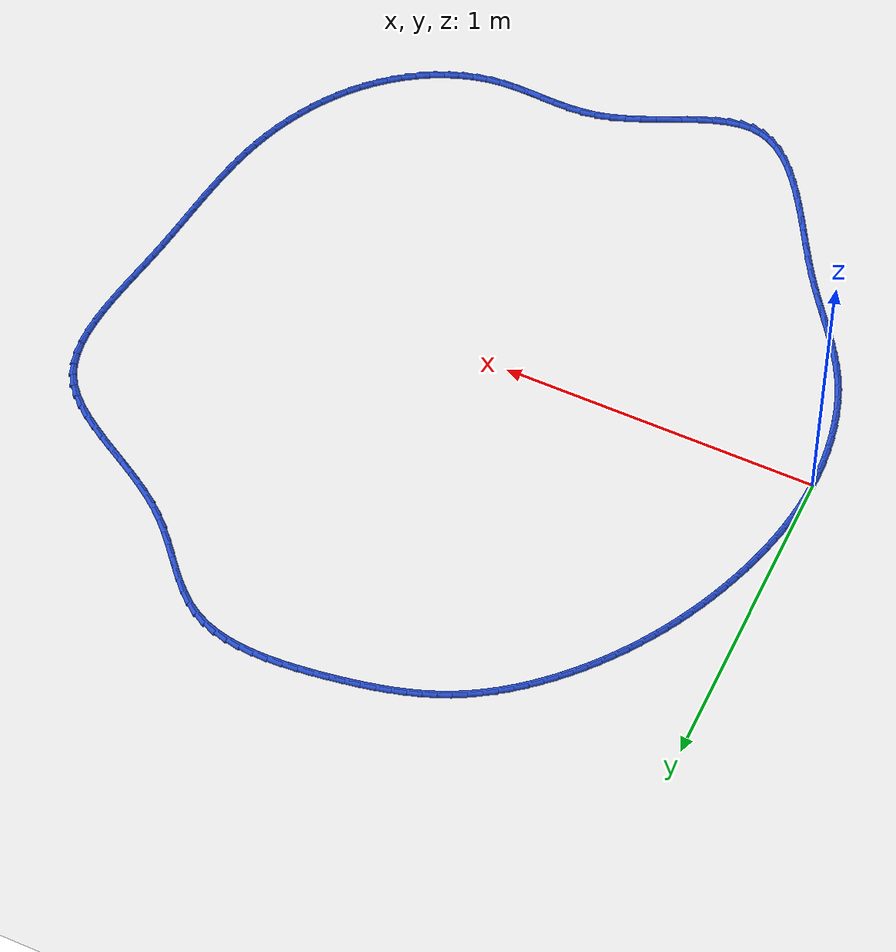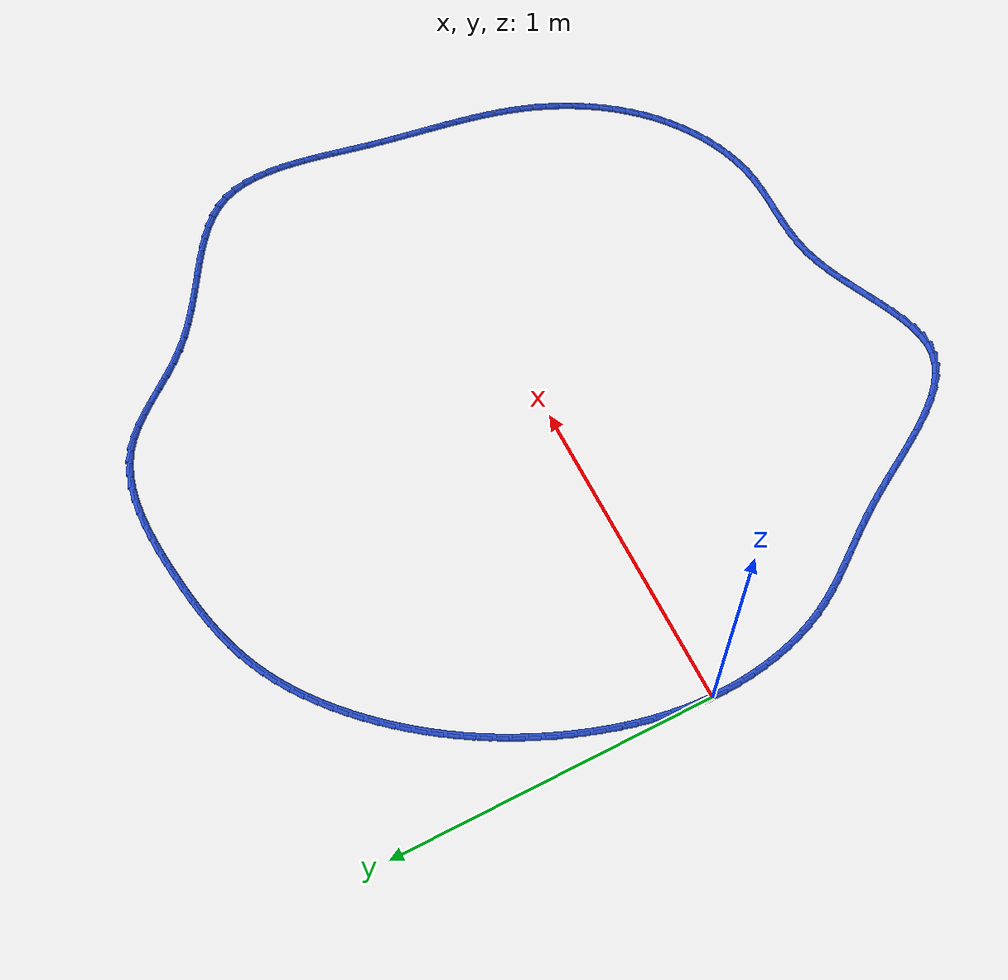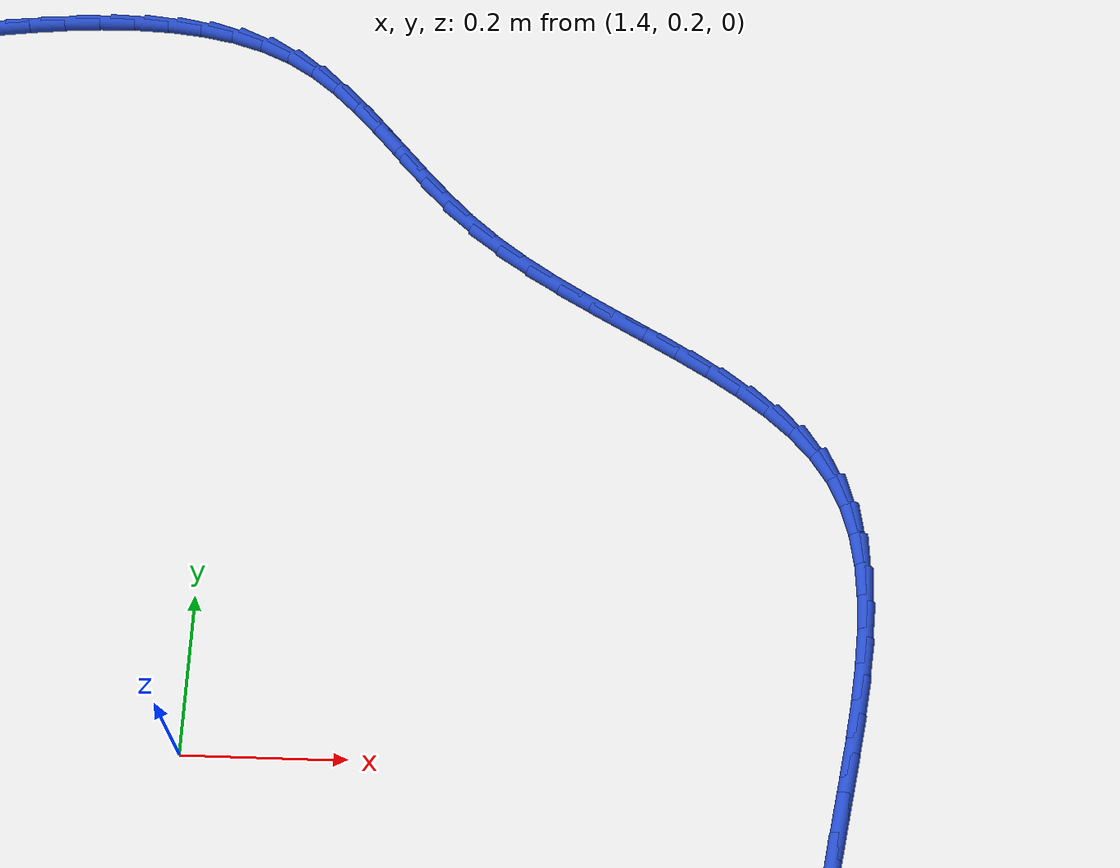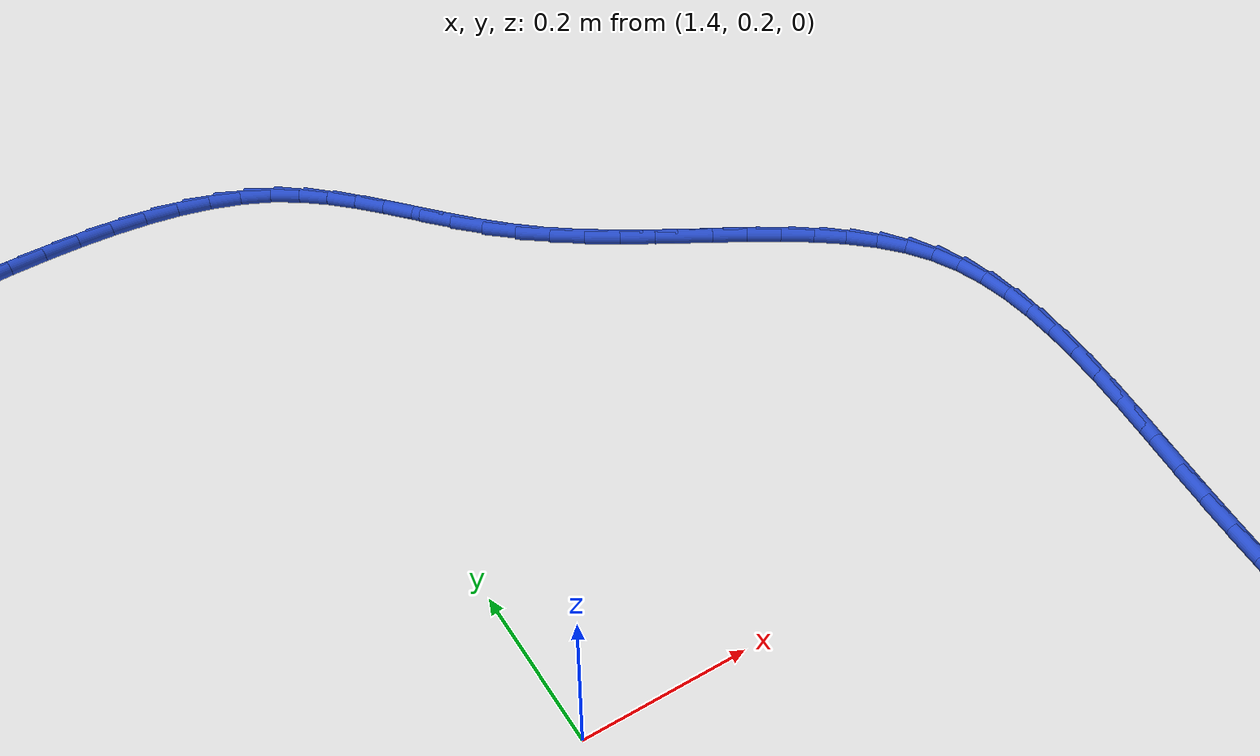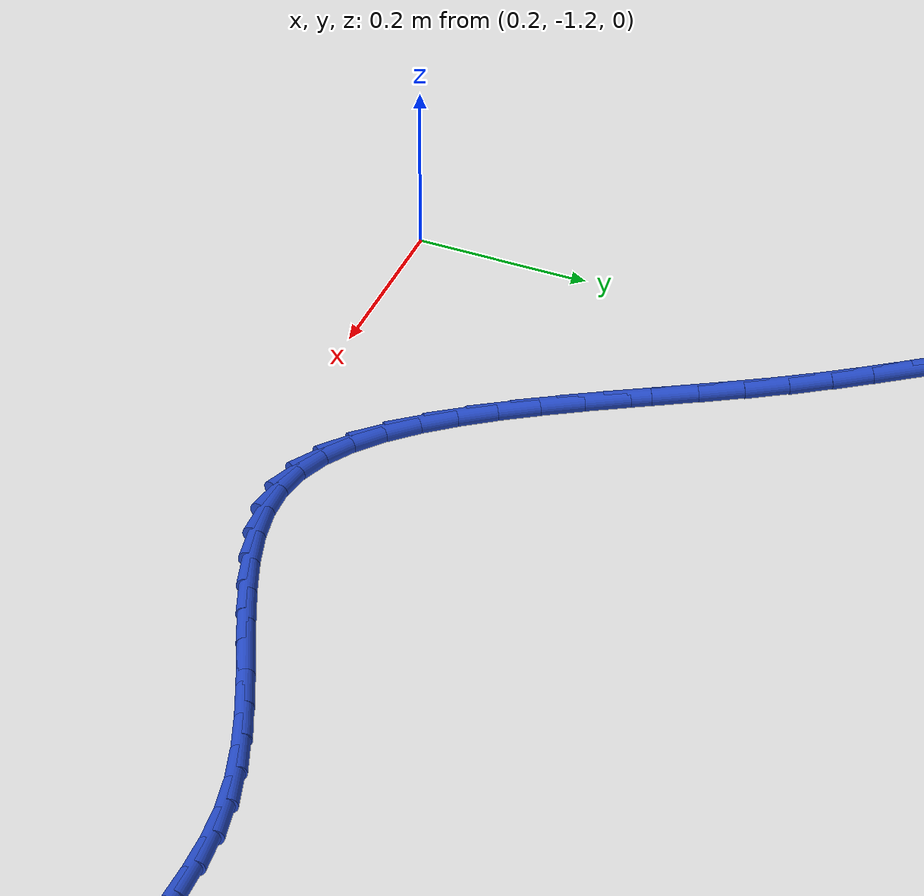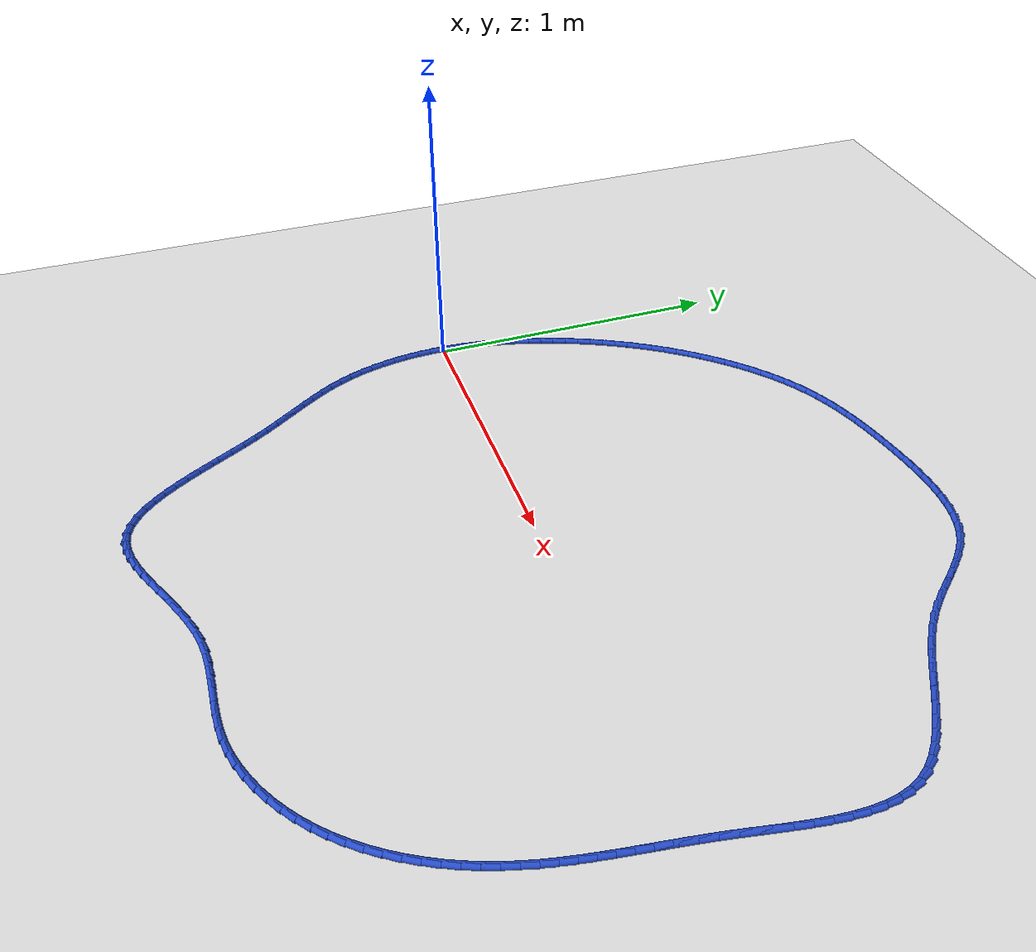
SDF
<sdf version="1.6">
 <world name="default">
  <light name="sun" type="directional">
   <pose>0 0 10 0 -0 0</pose>
   <diffuse>0.8 0.8 0.8 1</diffuse>
   <specular>0.2 0.2 0.2 1</specular>
   <attenuation>
    <range>1000</range>
    <constant>0.9</constant>
    <linear>0.01</linear>
    <quadratic>0.001</quadratic>
   </attenuation>
   <direction>-0.5 0.1 -0.9</direction>
  </light>
  <model name="ground_plane">
   <static>1</static>
   <link name="link">
    <collision name="collision">
     <geometry><plane><normal>0 0 1</normal><size>100 100</size></plane></geometry>
     <surface><friction><ode><mu>100</mu><mu2>50</mu2></ode></friction></surface>
    </collision>
    <visual name="visual">
     <cast_shadows>0</cast_shadows>
     <geometry><plane><normal>0 0 1</normal><size>100 100</size></plane></geometry>
     <material>
      <script><uri>file://media/materials/scripts/gazebo.material</uri><name>Gazebo/WhiteGlow</name></script>
     </material>
    </visual>
   </link>
  </model>
  <gravity>0 0 -9.8</gravity>
  <magnetic_field>6e-06 2.3e-05 -4.2e-05</magnetic_field>
  <atmosphere type="adiabatic"/>
  <physics name="default_physics" default="0" type="ode">
   <max_step_size>0.001</max_step_size>
   <real_time_factor>1</real_time_factor>
   <real_time_update_rate>1000</real_time_update_rate>
  </physics>
  <scene><ambient>0.4 0.4 0.4 1</ambient><background>0.7 0.7 0.7 1</background><shadows>1</shadows></scene>
  <spherical_coordinates>
   <surface_model>EARTH_WGS84</surface_model>
   <latitude_deg>0</latitude_deg>
   <longitude_deg>0</longitude_deg>
   <elevation>0</elevation>
   <heading_deg>0</heading_deg>
  </spherical_coordinates>
  <model name="line">
   <link name="link_0">
    <pose>-2.0816681711721685e-17 0.0 0.01 0 1.57 1.5288816077750744</pose>
    <collision name="collision">
     <geometry><cylinder><radius>0.01</radius><length>0.08</length></cylinder></geometry>
    </collision>
    <visual name="visual">
     <material>
      <script><name>Gazebo/Blue</name><uri>file://media/materials/scripts/gazebo.material</uri></script>
     </material>
     <geometry><cylinder><radius>0.01</radius><length>0.08</length></cylinder></geometry>
    </visual>
   </link>
   <link name="link_1">
    <pose>0.0018986274783184306 0.045270862564657524 0.01 0 1.57 1.4842349211723058</pose>
    <collision name="collision">
     <geometry><cylinder><radius>0.01</radius><length>0.08</length></cylinder></geometry>
    </collision>
    <visual name="visual">
     <material>
      <script><name>Gazebo/Blue</name><uri>file://media/materials/scripts/gazebo.material</uri></script>
     </material>
     <geometry><cylinder><radius>0.01</radius><length>0.08</length></cylinder></geometry>
    </visual>
   </link>
   <link name="link_2">
    <pose>0.005796107628394718 0.090183959916255 0.01 0 1.57 1.4415043445787512</pose>
    <collision name="collision">
     <geometry><cylinder><radius>0.01</radius><length>0.08</length></cylinder></geometry>
    </collision>
    <visual name="visual">
     <material>
      <script><name>Gazebo/Blue</name><uri>file://media/materials/scripts/gazebo.material</uri></script>
     </material>
     <geometry><cylinder><radius>0.01</radius><length>0.08</length></cylinder></geometry>
    </visual>
   </link>
   <link name="link_3">
    <pose>0.01158838810931956 0.13473404697442215 0.01 0 1.57 1.400820167385126</pose>
    <collision name="collision">
     <geometry><cylinder><radius>0.01</radius><length>0.08</length></cylinder></geometry>
    </collision>
    <visual name="visual">
     <material>
      <script><name>Gazebo/Blue</name><uri>file://media/materials/scripts/gazebo.material</uri></script>
     </material>
     <geometry><cylinder><radius>0.01</radius><length>0.08</length></cylinder></geometry>
    </visual>
   </link>
   <link name="link_4">
    <pose>0.01917141658018367 0.1789158786587886 0.01 0 1.57 1.3622748014016555</pose>
    <collision name="collision">
     <geometry><cylinder><radius>0.01</radius><length>0.08</length></cylinder></geometry>
    </collision>
    <visual name="visual">
     <material>
      <script><name>Gazebo/Blue</name><uri>file://media/materials/scripts/gazebo.material</uri></script>
     </material>
     <geometry><cylinder><radius>0.01</radius><length>0.08</length></cylinder></geometry>
    </visual>
   </link>
   <link name="link_5">
    <pose>0.028441140700077774 0.22272420988898411 0.01 0 1.57 1.325926651619005</pose>
    <collision name="collision">
     <geometry><cylinder><radius>0.01</radius><length>0.08</length></cylinder></geometry>
    </collision>
    <visual name="visual">
     <material>
      <script><name>Gazebo/Blue</name><uri>file://media/materials/scripts/gazebo.material</uri></script>
     </material>
     <geometry><cylinder><radius>0.01</radius><length>0.08</length></cylinder></geometry>
    </visual>
   </link>
   <link name="link_6">
    <pose>0.039293508128092576 0.26615379558463836 0.01 0 1.57 1.2918048528921524</pose>
    <collision name="collision">
     <geometry><cylinder><radius>0.01</radius><length>0.08</length></cylinder></geometry>
    </collision>
    <visual name="visual">
     <material>
      <script><name>Gazebo/Blue</name><uri>file://media/materials/scripts/gazebo.material</uri></script>
     </material>
     <geometry><cylinder><radius>0.01</radius><length>0.08</length></cylinder></geometry>
    </visual>
   </link>
   <link name="link_7">
    <pose>0.051624466523318806 0.30919939066538094 0.01 0 1.57 1.2599143963918624</pose>
    <collision name="collision">
     <geometry><cylinder><radius>0.01</radius><length>0.08</length></cylinder></geometry>
    </collision>
    <visual name="visual">
     <material>
      <script><name>Gazebo/Blue</name><uri>file://media/materials/scripts/gazebo.material</uri></script>
     </material>
     <geometry><cylinder><radius>0.01</radius><length>0.08</length></cylinder></geometry>
    </visual>
   </link>
   <link name="link_8">
    <pose>0.06532996354484717 0.3518557500508417 0.01 0 1.57 1.2302329889675874</pose>
    <collision name="collision">
     <geometry><cylinder><radius>0.01</radius><length>0.08</length></cylinder></geometry>
    </collision>
    <visual name="visual">
     <material>
      <script><name>Gazebo/Blue</name><uri>file://media/materials/scripts/gazebo.material</uri></script>
     </material>
     <geometry><cylinder><radius>0.01</radius><length>0.08</length></cylinder></geometry>
    </visual>
   </link>
   <link name="link_9">
    <pose>0.080306294159341 0.394117497454117 0.01 0 1.57 1.201915558746725</pose>
    <collision name="collision">
     <geometry><cylinder><radius>0.01</radius><length>0.08</length></cylinder></geometry>
    </collision>
    <visual name="visual">
     <material>
      <script><name>Gazebo/Blue</name><uri>file://media/materials/scripts/gazebo.material</uri></script>
     </material>
     <geometry><cylinder><radius>0.01</radius><length>0.08</length></cylinder></geometry>
    </visual>
   </link>
   <link name="link_10">
    <pose>0.09648404263138836 0.43596630271035763 0.01 0 1.57 1.1734323717533908</pose>
    <collision name="collision">
     <geometry><cylinder><radius>0.01</radius><length>0.08</length></cylinder></geometry>
    </collision>
    <visual name="visual">
     <material>
      <script><name>Gazebo/Blue</name><uri>file://media/materials/scripts/gazebo.material</uri></script>
     </material>
     <geometry><cylinder><radius>0.01</radius><length>0.08</length></cylinder></geometry>
    </visual>
   </link>
   <link name="link_11">
    <pose>0.1138565870593402 0.4773601132775439 0.01 0 1.57 1.1445915852036095</pose>
    <collision name="collision">
     <geometry><cylinder><radius>0.01</radius><length>0.08</length></cylinder></geometry>
    </collision>
    <visual name="visual">
     <material>
      <script><name>Gazebo/Blue</name><uri>file://media/materials/scripts/gazebo.material</uri></script>
     </material>
     <geometry><cylinder><radius>0.01</radius><length>0.08</length></cylinder></geometry>
    </visual>
   </link>
   <link name="link_12">
    <pose>0.13242401652353475 0.5182543413257723 0.01 0 1.57 1.1153630447372038</pose>
    <collision name="collision">
     <geometry><cylinder><radius>0.01</radius><length>0.08</length></cylinder></geometry>
    </collision>
    <visual name="visual">
     <material>
      <script><name>Gazebo/Blue</name><uri>file://media/materials/scripts/gazebo.material</uri></script>
     </material>
     <geometry><cylinder><radius>0.01</radius><length>0.08</length></cylinder></geometry>
    </visual>
   </link>
   <link name="link_13">
    <pose>0.15218642010431016 0.558604399025139 0.01 0 1.57 1.0857185533105422</pose>
    <collision name="collision">
     <geometry><cylinder><radius>0.01</radius><length>0.08</length></cylinder></geometry>
    </collision>
    <visual name="visual">
     <material>
      <script><name>Gazebo/Blue</name><uri>file://media/materials/scripts/gazebo.material</uri></script>
     </material>
     <geometry><cylinder><radius>0.01</radius><length>0.08</length></cylinder></geometry>
    </visual>
   </link>
   <link name="link_14">
    <pose>0.17314388688200485 0.5983656985457407 0.01 0 1.57 1.0556321395603914</pose>
    <collision name="collision">
     <geometry><cylinder><radius>0.01</radius><length>0.08</length></cylinder></geometry>
    </collision>
    <visual name="visual">
     <material>
      <script><name>Gazebo/Blue</name><uri>file://media/materials/scripts/gazebo.material</uri></script>
     </material>
     <geometry><cylinder><radius>0.01</radius><length>0.08</length></cylinder></geometry>
    </visual>
   </link>
   <link name="link_15">
    <pose>0.1952965059369569 0.6374936520576736 0.01 0 1.57 1.0250803586333848</pose>
    <collision name="collision">
     <geometry><cylinder><radius>0.01</radius><length>0.08</length></cylinder></geometry>
    </collision>
    <visual name="visual">
     <material>
      <script><name>Gazebo/Blue</name><uri>file://media/materials/scripts/gazebo.material</uri></script>
     </material>
     <geometry><cylinder><radius>0.01</radius><length>0.08</length></cylinder></geometry>
    </visual>
   </link>
   <link name="link_16">
    <pose>0.21864436634950482 0.6759436717310348 0.01 0 1.57 0.9940426239044867</pose>
    <collision name="collision">
     <geometry><cylinder><radius>0.01</radius><length>0.08</length></cylinder></geometry>
    </collision>
    <visual name="visual">
     <material>
      <script><name>Gazebo/Blue</name><uri>file://media/materials/scripts/gazebo.material</uri></script>
     </material>
     <geometry><cylinder><radius>0.01</radius><length>0.08</length></cylinder></geometry>
    </visual>
   </link>
   <link name="link_17">
    <pose>0.24318755719998664 0.7136711697359202 0.01 0 1.57 0.9625015665755179</pose>
    <collision name="collision">
     <geometry><cylinder><radius>0.01</radius><length>0.08</length></cylinder></geometry>
    </collision>
    <visual name="visual">
     <material>
      <script><name>Gazebo/Blue</name><uri>file://media/materials/scripts/gazebo.material</uri></script>
     </material>
     <geometry><cylinder><radius>0.01</radius><length>0.08</length></cylinder></geometry>
    </visual>
   </link>
   <link name="link_18">
    <pose>0.26892616756874066 0.7506315582424266 0.01 0 1.57 0.9304434184569393</pose>
    <collision name="collision">
     <geometry><cylinder><radius>0.01</radius><length>0.08</length></cylinder></geometry>
    </collision>
    <visual name="visual">
     <material>
      <script><name>Gazebo/Blue</name><uri>file://media/materials/scripts/gazebo.material</uri></script>
     </material>
     <geometry><cylinder><radius>0.01</radius><length>0.08</length></cylinder></geometry>
    </visual>
   </link>
   <link name="link_19">
    <pose>0.2958602865361052 0.7867802494206502 0.01 0 1.57 0.8978584113109714</pose>
    <collision name="collision">
     <geometry><cylinder><radius>0.01</radius><length>0.08</length></cylinder></geometry>
    </collision>
    <visual name="visual">
     <material>
      <script><name>Gazebo/Blue</name><uri>file://media/materials/scripts/gazebo.material</uri></script>
     </material>
     <geometry><cylinder><radius>0.01</radius><length>0.08</length></cylinder></geometry>
    </visual>
   </link>
   <link name="link_20">
    <pose>0.3239900031824186 0.8220726554406879 0.01 0 1.57 0.8647411840159512</pose>
    <collision name="collision">
     <geometry><cylinder><radius>0.01</radius><length>0.08</length></cylinder></geometry>
    </collision>
    <visual name="visual">
     <material>
      <script><name>Gazebo/Blue</name><uri>file://media/materials/scripts/gazebo.material</uri></script>
     </material>
     <geometry><cylinder><radius>0.01</radius><length>0.08</length></cylinder></geometry>
    </visual>
   </link>
   <link name="link_21">
    <pose>0.35331540658801897 0.8564641884726361 0.01 0 1.57 0.8310911865787765</pose>
    <collision name="collision">
     <geometry><cylinder><radius>0.01</radius><length>0.08</length></cylinder></geometry>
    </collision>
    <visual name="visual">
     <material>
      <script><name>Gazebo/Blue</name><uri>file://media/materials/scripts/gazebo.material</uri></script>
     </material>
     <geometry><cylinder><radius>0.01</radius><length>0.08</length></cylinder></geometry>
    </visual>
   </link>
   <link name="link_22">
    <pose>0.38383658583324465 0.889910260686591 0.01 0 1.57 0.7966848038473127</pose>
    <collision name="collision">
     <geometry><cylinder><radius>0.01</radius><length>0.08</length></cylinder></geometry>
    </collision>
    <visual name="visual">
     <material>
      <script><name>Gazebo/Blue</name><uri>file://media/materials/scripts/gazebo.material</uri></script>
     </material>
     <geometry><cylinder><radius>0.01</radius><length>0.08</length></cylinder></geometry>
    </visual>
   </link>
   <link name="link_23">
    <pose>0.41554763064454986 0.9223453303728348 0.01 0 1.57 0.7604444711862371</pose>
    <collision name="collision">
     <geometry><cylinder><radius>0.01</radius><length>0.08</length></cylinder></geometry>
    </collision>
    <visual name="visual">
     <material>
      <script><name>Gazebo/Blue</name><uri>file://media/materials/scripts/gazebo.material</uri></script>
     </material>
     <geometry><cylinder><radius>0.01</radius><length>0.08</length></cylinder></geometry>
    </visual>
   </link>
   <link name="link_24">
    <pose>0.4484168244058946 0.953613722282348 0.01 0 1.57 0.7218498556387832</pose>
    <collision name="collision">
     <geometry><cylinder><radius>0.01</radius><length>0.08</length></cylinder></geometry>
    </collision>
    <visual name="visual">
     <material>
      <script><name>Gazebo/Blue</name><uri>file://media/materials/scripts/gazebo.material</uri></script>
     </material>
     <geometry><cylinder><radius>0.01</radius><length>0.08</length></cylinder></geometry>
    </visual>
   </link>
   <link name="link_25">
    <pose>0.4824055131075488 0.9835355310045948 0.01 0 1.57 0.6806194166021386</pose>
    <collision name="collision">
     <geometry><cylinder><radius>0.01</radius><length>0.08</length></cylinder></geometry>
    </collision>
    <visual name="visual">
     <material>
      <script><name>Gazebo/Blue</name><uri>file://media/materials/scripts/gazebo.material</uri></script>
     </material>
     <geometry><cylinder><radius>0.01</radius><length>0.08</length></cylinder></geometry>
    </visual>
   </link>
   <link name="link_26">
    <pose>0.5174750426480814 1.0119308508087546 0.01 0 1.57 0.6364662482229534</pose>
    <collision name="collision">
     <geometry><cylinder><radius>0.01</radius><length>0.08</length></cylinder></geometry>
    </collision>
    <visual name="visual">
     <material>
      <script><name>Gazebo/Blue</name><uri>file://media/materials/scripts/gazebo.material</uri></script>
     </material>
     <geometry><cylinder><radius>0.01</radius><length>0.08</length></cylinder></geometry>
    </visual>
   </link>
   <link name="link_27">
    <pose>0.5535867589260608 1.0386197759640066 0.01 0 1.57 0.5891046559166444</pose>
    <collision name="collision">
     <geometry><cylinder><radius>0.01</radius><length>0.08</length></cylinder></geometry>
    </collision>
    <visual name="visual">
     <material>
      <script><name>Gazebo/Blue</name><uri>file://media/materials/scripts/gazebo.material</uri></script>
     </material>
     <geometry><cylinder><radius>0.01</radius><length>0.08</length></cylinder></geometry>
    </visual>
   </link>
   <link name="link_28">
    <pose>0.5907020078400552 1.0634224007395292 0.01 0 1.57 0.5382606959549727</pose>
    <collision name="collision">
     <geometry><cylinder><radius>0.01</radius><length>0.08</length></cylinder></geometry>
    </collision>
    <visual name="visual">
     <material>
      <script><name>Gazebo/Blue</name><uri>file://media/materials/scripts/gazebo.material</uri></script>
     </material>
     <geometry><cylinder><radius>0.01</radius><length>0.08</length></cylinder></geometry>
    </visual>
   </link>
   <link name="link_29">
    <pose>0.6287821352886335 1.0861588194045018 0.01 0 1.57 0.4837081633255312</pose>
    <collision name="collision">
     <geometry><cylinder><radius>0.01</radius><length>0.08</length></cylinder></geometry>
    </collision>
    <visual name="visual">
     <material>
      <script><name>Gazebo/Blue</name><uri>file://media/materials/scripts/gazebo.material</uri></script>
     </material>
     <geometry><cylinder><radius>0.01</radius><length>0.08</length></cylinder></geometry>
    </visual>
   </link>
   <link name="link_30">
    <pose>0.6677885769691463 1.1066501978492853 0.01 0 1.57 0.4276677276523153</pose>
    <collision name="collision">
     <geometry><cylinder><radius>0.01</radius><length>0.08</length></cylinder></geometry>
    </collision>
    <visual name="visual">
     <material>
      <script><name>Gazebo/Blue</name><uri>file://media/materials/scripts/gazebo.material</uri></script>
     </material>
     <geometry><cylinder><radius>0.01</radius><length>0.08</length></cylinder></geometry>
    </visual>
   </link>
   <link name="link_31">
    <pose>0.7076929026458838 1.1248386376881985 0.01 0 1.57 0.3750144893814631</pose>
    <collision name="collision">
     <geometry><cylinder><radius>0.01</radius><length>0.08</length></cylinder></geometry>
    </collision>
    <visual name="visual">
     <material>
      <script><name>Gazebo/Blue</name><uri>file://media/materials/scripts/gazebo.material</uri></script>
     </material>
     <geometry><cylinder><radius>0.01</radius><length>0.08</length></cylinder></geometry>
    </visual>
   </link>
   <link name="link_32">
    <pose>0.7484859822427457 1.140896560582712 0.01 0 1.57 0.3267963278468307</pose>
    <collision name="collision">
     <geometry><cylinder><radius>0.01</radius><length>0.08</length></cylinder></geometry>
    </collision>
    <visual name="visual">
     <material>
      <script><name>Gazebo/Blue</name><uri>file://media/materials/scripts/gazebo.material</uri></script>
     </material>
     <geometry><cylinder><radius>0.01</radius><length>0.08</length></cylinder></geometry>
    </visual>
   </link>
   <link name="link_33">
    <pose>0.7901608507896076 1.1550222256650946 0.01 0 1.57 0.28338988487106853</pose>
    <collision name="collision">
     <geometry><cylinder><radius>0.01</radius><length>0.08</length></cylinder></geometry>
    </collision>
    <visual name="visual">
     <material>
      <script><name>Gazebo/Blue</name><uri>file://media/materials/scripts/gazebo.material</uri></script>
     </material>
     <geometry><cylinder><radius>0.01</radius><length>0.08</length></cylinder></geometry>
    </visual>
   </link>
   <link name="link_34">
    <pose>0.8327105433163452 1.1674138920676156 0.01 0 1.57 0.2450120236223205</pose>
    <collision name="collision">
     <geometry><cylinder><radius>0.01</radius><length>0.08</length></cylinder></geometry>
    </collision>
    <visual name="visual">
     <material>
      <script><name>Gazebo/Blue</name><uri>file://media/materials/scripts/gazebo.material</uri></script>
     </material>
     <geometry><cylinder><radius>0.01</radius><length>0.08</length></cylinder></geometry>
    </visual>
   </link>
   <link name="link_35">
    <pose>0.8761280948528342 1.1782698189225438 0.01 0 1.57 0.2117455207977764</pose>
    <collision name="collision">
     <geometry><cylinder><radius>0.01</radius><length>0.08</length></cylinder></geometry>
    </collision>
    <visual name="visual">
     <material>
      <script><name>Gazebo/Blue</name><uri>file://media/materials/scripts/gazebo.material</uri></script>
     </material>
     <geometry><cylinder><radius>0.01</radius><length>0.08</length></cylinder></geometry>
    </visual>
   </link>
   <link name="link_36">
    <pose>0.9204065404289501 1.1877882653621483 0.01 0 1.57 0.18356874632697723</pose>
    <collision name="collision">
     <geometry><cylinder><radius>0.01</radius><length>0.08</length></cylinder></geometry>
    </collision>
    <visual name="visual">
     <material>
      <script><name>Gazebo/Blue</name><uri>file://media/materials/scripts/gazebo.material</uri></script>
     </material>
     <geometry><cylinder><radius>0.01</radius><length>0.08</length></cylinder></geometry>
    </visual>
   </link>
   <link name="link_37">
    <pose>0.9655389150745686 1.1961674905186972 0.01 0 1.57 0.16038453201115208</pose>
    <collision name="collision">
     <geometry><cylinder><radius>0.01</radius><length>0.08</length></cylinder></geometry>
    </collision>
    <visual name="visual">
     <material>
      <script><name>Gazebo/Blue</name><uri>file://media/materials/scripts/gazebo.material</uri></script>
     </material>
     <geometry><cylinder><radius>0.01</radius><length>0.08</length></cylinder></geometry>
    </visual>
   </link>
   <link name="link_38">
    <pose>1.011518253819565 1.2036057535244598 0.01 0 1.57 0.14166314754316453</pose>
    <collision name="collision">
     <geometry><cylinder><radius>0.01</radius><length>0.08</length></cylinder></geometry>
    </collision>
    <visual name="visual">
     <material>
      <script><name>Gazebo/Blue</name><uri>file://media/materials/scripts/gazebo.material</uri></script>
     </material>
     <geometry><cylinder><radius>0.01</radius><length>0.08</length></cylinder></geometry>
    </visual>
   </link>
   <link name="link_39">
    <pose>1.0583256229354534 1.2102813488996835 0.01 0 1.57 0.12074123063330013</pose>
    <collision name="collision">
     <geometry><cylinder><radius>0.01</radius><length>0.08</length></cylinder></geometry>
    </collision>
    <visual name="visual">
     <material>
      <script><name>Gazebo/Blue</name><uri>file://media/materials/scripts/gazebo.material</uri></script>
     </material>
     <geometry><cylinder><radius>0.01</radius><length>0.08</length></cylinder></geometry>
    </visual>
   </link>
   <link name="link_40">
    <pose>1.1057391771114726 1.2160341023867947 0.01 0 1.57 0.09185437337763562</pose>
    <collision name="collision">
     <geometry><cylinder><radius>0.01</radius><length>0.08</length></cylinder></geometry>
    </collision>
    <visual name="visual">
     <material>
      <script><name>Gazebo/Blue</name><uri>file://media/materials/scripts/gazebo.material</uri></script>
     </material>
     <geometry><cylinder><radius>0.01</radius><length>0.08</length></cylinder></geometry>
    </visual>
   </link>
   <link name="link_41">
    <pose>1.1533677111331038 1.2204213371771335 0.01 0 1.57 0.054120727202297464</pose>
    <collision name="collision">
     <geometry><cylinder><radius>0.01</radius><length>0.08</length></cylinder></geometry>
    </collision>
    <visual name="visual">
     <material>
      <script><name>Gazebo/Blue</name><uri>file://media/materials/scripts/gazebo.material</uri></script>
     </material>
     <geometry><cylinder><radius>0.01</radius><length>0.08</length></cylinder></geometry>
    </visual>
   </link>
   <link name="link_42">
    <pose>1.2008148301574335 1.2229917198483584 0.01 0 1.57 0.006447565527677258</pose>
    <collision name="collision">
     <geometry><cylinder><radius>0.01</radius><length>0.08</length></cylinder></geometry>
    </collision>
    <visual name="visual">
     <material>
      <script><name>Gazebo/Blue</name><uri>file://media/materials/scripts/gazebo.material</uri></script>
     </material>
     <geometry><cylinder><radius>0.01</radius><length>0.08</length></cylinder></geometry>
    </visual>
   </link>
   <link name="link_43">
    <pose>1.2476841393415485 1.2232939169781274 0.01 0 1.57 -0.05262195616733427</pose>
    <collision name="collision">
     <geometry><cylinder><radius>0.01</radius><length>0.08</length></cylinder></geometry>
    </collision>
    <visual name="visual">
     <material>
      <script><name>Gazebo/Blue</name><uri>file://media/materials/scripts/gazebo.material</uri></script>
     </material>
     <geometry><cylinder><radius>0.01</radius><length>0.08</length></cylinder></geometry>
    </visual>
   </link>
   <link name="link_44">
    <pose>1.2935792438425382 1.220876595144099 0.01 0 1.57 -0.12485498532663875</pose>
    <collision name="collision">
     <geometry><cylinder><radius>0.01</radius><length>0.08</length></cylinder></geometry>
    </collision>
    <visual name="visual">
     <material>
      <script><name>Gazebo/Blue</name><uri>file://media/materials/scripts/gazebo.material</uri></script>
     </material>
     <geometry><cylinder><radius>0.01</radius><length>0.08</length></cylinder></geometry>
    </visual>
   </link>
   <link name="link_45">
    <pose>1.3381037488174883 1.2152884209239316 0.01 0 1.57 -0.2121672224260136</pose>
    <collision name="collision">
     <geometry><cylinder><radius>0.01</radius><length>0.08</length></cylinder></geometry>
    </collision>
    <visual name="visual">
     <material>
      <script><name>Gazebo/Blue</name><uri>file://media/materials/scripts/gazebo.material</uri></script>
     </material>
     <geometry><cylinder><radius>0.01</radius><length>0.08</length></cylinder></geometry>
    </visual>
   </link>
   <link name="link_46">
    <pose>1.3808612594234875 1.2060780608952835 0.01 0 1.57 -0.3162534285574934</pose>
    <collision name="collision">
     <geometry><cylinder><radius>0.01</radius><length>0.08</length></cylinder></geometry>
    </collision>
    <visual name="visual">
     <material>
      <script><name>Gazebo/Blue</name><uri>file://media/materials/scripts/gazebo.material</uri></script>
     </material>
     <geometry><cylinder><radius>0.01</radius><length>0.08</length></cylinder></geometry>
    </visual>
   </link>
   <link name="link_47">
    <pose>1.4214553808176222 1.192794181635813 0.01 0 1.57 -0.43790829810327386</pose>
    <collision name="collision">
     <geometry><cylinder><radius>0.01</radius><length>0.08</length></cylinder></geometry>
    </collision>
    <visual name="visual">
     <material>
      <script><name>Gazebo/Blue</name><uri>file://media/materials/scripts/gazebo.material</uri></script>
     </material>
     <geometry><cylinder><radius>0.01</radius><length>0.08</length></cylinder></geometry>
    </visual>
   </link>
   <link name="link_48">
    <pose>1.4594897181569801 1.1749854497231775 0.01 0 1.57 -0.5723241459038471</pose>
    <collision name="collision">
     <geometry><cylinder><radius>0.01</radius><length>0.08</length></cylinder></geometry>
    </collision>
    <visual name="visual">
     <material>
      <script><name>Gazebo/Blue</name><uri>file://media/materials/scripts/gazebo.material</uri></script>
     </material>
     <geometry><cylinder><radius>0.01</radius><length>0.08</length></cylinder></geometry>
    </visual>
   </link>
   <link name="link_49">
    <pose>1.4946665700119324 1.152322676758436 0.01 0 1.57 -0.6892413904597401</pose>
    <collision name="collision">
     <geometry><cylinder><radius>0.01</radius><length>0.08</length></cylinder></geometry>
    </collision>
    <visual name="visual">
     <material>
      <script><name>Gazebo/Blue</name><uri>file://media/materials/scripts/gazebo.material</uri></script>
     </material>
     <geometry><cylinder><radius>0.01</radius><length>0.08</length></cylinder></geometry>
    </visual>
   </link>
   <link name="link_50">
    <pose>1.5273955115844915 1.1253520146297842 0.01 0 1.57 -0.7748260927825578</pose>
    <collision name="collision">
     <geometry><cylinder><radius>0.01</radius><length>0.08</length></cylinder></geometry>
    </collision>
    <visual name="visual">
     <material>
      <script><name>Gazebo/Blue</name><uri>file://media/materials/scripts/gazebo.material</uri></script>
     </material>
     <geometry><cylinder><radius>0.01</radius><length>0.08</length></cylinder></geometry>
    </visual>
   </link>
   <link name="link_51">
    <pose>1.558394664686706 1.0950014789349503 0.01 0 1.57 -0.8301533373716767</pose>
    <collision name="collision">
     <geometry><cylinder><radius>0.01</radius><length>0.08</length></cylinder></geometry>
    </collision>
    <visual name="visual">
     <material>
      <script><name>Gazebo/Blue</name><uri>file://media/materials/scripts/gazebo.material</uri></script>
     </material>
     <geometry><cylinder><radius>0.01</radius><length>0.08</length></cylinder></geometry>
    </visual>
   </link>
   <link name="link_52">
    <pose>1.5883834342252279 1.0622006732562608 0.01 0 1.57 -0.8574962585744776</pose>
    <collision name="collision">
     <geometry><cylinder><radius>0.01</radius><length>0.08</length></cylinder></geometry>
    </collision>
    <visual name="visual">
     <material>
      <script><name>Gazebo/Blue</name><uri>file://media/materials/scripts/gazebo.material</uri></script>
     </material>
     <geometry><cylinder><radius>0.01</radius><length>0.08</length></cylinder></geometry>
    </visual>
   </link>
   <link name="link_53">
    <pose>1.6180812251067078 1.0278792011760416 0.01 0 1.57 -0.8588575254970319</pose>
    <collision name="collision">
     <geometry><cylinder><radius>0.01</radius><length>0.08</length></cylinder></geometry>
    </collision>
    <visual name="visual">
     <material>
      <script><name>Gazebo/Blue</name><uri>file://media/materials/scripts/gazebo.material</uri></script>
     </material>
     <geometry><cylinder><radius>0.01</radius><length>0.08</length></cylinder></geometry>
    </visual>
   </link>
   <link name="link_54">
    <pose>1.6482074422377968 0.9929666662766191 0.01 0 1.57 -0.8354708354467425</pose>
    <collision name="collision">
     <geometry><cylinder><radius>0.01</radius><length>0.08</length></cylinder></geometry>
    </collision>
    <visual name="visual">
     <material>
      <script><name>Gazebo/Blue</name><uri>file://media/materials/scripts/gazebo.material</uri></script>
     </material>
     <geometry><cylinder><radius>0.01</radius><length>0.08</length></cylinder></geometry>
    </visual>
   </link>
   <link name="link_55">
    <pose>1.6794814905251454 0.9583926721403192 0.01 0 1.57 -0.7878747954787787</pose>
    <collision name="collision">
     <geometry><cylinder><radius>0.01</radius><length>0.08</length></cylinder></geometry>
    </collision>
    <visual name="visual">
     <material>
      <script><name>Gazebo/Blue</name><uri>file://media/materials/scripts/gazebo.material</uri></script>
     </material>
     <geometry><cylinder><radius>0.01</radius><length>0.08</length></cylinder></geometry>
    </visual>
   </link>
   <link name="link_56">
    <pose>1.712622774875405 0.9250868223494677 0.01 0 1.57 -0.7176364242600842</pose>
    <collision name="collision">
     <geometry><cylinder><radius>0.01</radius><length>0.08</length></cylinder></geometry>
    </collision>
    <visual name="visual">
     <material>
      <script><name>Gazebo/Blue</name><uri>file://media/materials/scripts/gazebo.material</uri></script>
     </material>
     <geometry><cylinder><radius>0.01</radius><length>0.08</length></cylinder></geometry>
    </visual>
   </link>
   <link name="link_57">
    <pose>1.7483084609158623 0.8939369728865907 0.01 0 1.57 -0.6465781644613865</pose>
    <collision name="collision">
     <geometry><cylinder><radius>0.01</radius><length>0.08</length></cylinder></geometry>
    </collision>
    <visual name="visual">
     <material>
      <script><name>Gazebo/Blue</name><uri>file://media/materials/scripts/gazebo.material</uri></script>
     </material>
     <geometry><cylinder><radius>0.01</radius><length>0.08</length></cylinder></geometry>
    </visual>
   </link>
   <link name="link_58">
    <pose>1.7864917825711828 0.8651154748425918 0.01 0 1.57 -0.5921116740411578</pose>
    <collision name="collision">
     <geometry><cylinder><radius>0.01</radius><length>0.08</length></cylinder></geometry>
    </collision>
    <visual name="visual">
     <material>
      <script><name>Gazebo/Blue</name><uri>file://media/materials/scripts/gazebo.material</uri></script>
     </material>
     <geometry><cylinder><radius>0.01</radius><length>0.08</length></cylinder></geometry>
    </visual>
   </link>
   <link name="link_59">
    <pose>1.8265175935123321 0.8381933808075479 0.01 0 1.57 -0.553765520842661</pose>
    <collision name="collision">
     <geometry><cylinder><radius>0.01</radius><length>0.08</length></cylinder></geometry>
    </collision>
    <visual name="visual">
     <material>
      <script><name>Gazebo/Blue</name><uri>file://media/materials/scripts/gazebo.material</uri></script>
     </material>
     <geometry><cylinder><radius>0.01</radius><length>0.08</length></cylinder></geometry>
    </visual>
   </link>
   <link name="link_60">
    <pose>1.867711837717998 0.8127230537944989 0.01 0 1.57 -0.530716203560321</pose>
    <collision name="collision">
     <geometry><cylinder><radius>0.01</radius><length>0.08</length></cylinder></geometry>
    </collision>
    <visual name="visual">
     <material>
      <script><name>Gazebo/Blue</name><uri>file://media/materials/scripts/gazebo.material</uri></script>
     </material>
     <geometry><cylinder><radius>0.01</radius><length>0.08</length></cylinder></geometry>
    </visual>
   </link>
   <link name="link_61">
    <pose>1.9094004591668672 0.788256856816485 0.01 0 1.57 -0.5225954841695842</pose>
    <collision name="collision">
     <geometry><cylinder><radius>0.01</radius><length>0.08</length></cylinder></geometry>
    </collision>
    <visual name="visual">
     <material>
      <script><name>Gazebo/Blue</name><uri>file://media/materials/scripts/gazebo.material</uri></script>
     </material>
     <geometry><cylinder><radius>0.01</radius><length>0.08</length></cylinder></geometry>
    </visual>
   </link>
   <link name="link_62">
    <pose>1.9509094018376265 0.7643471528865464 0.01 0 1.57 -0.5296386468588618</pose>
    <collision name="collision">
     <geometry><cylinder><radius>0.01</radius><length>0.08</length></cylinder></geometry>
    </collision>
    <visual name="visual">
     <material>
      <script><name>Gazebo/Blue</name><uri>file://media/materials/scripts/gazebo.material</uri></script>
     </material>
     <geometry><cylinder><radius>0.01</radius><length>0.08</length></cylinder></geometry>
    </visual>
   </link>
   <link name="link_63">
    <pose>1.9915646097089637 0.7405463050177229 0.01 0 1.57 -0.5527890202759829</pose>
    <collision name="collision">
     <geometry><cylinder><radius>0.01</radius><length>0.08</length></cylinder></geometry>
    </collision>
    <visual name="visual">
     <material>
      <script><name>Gazebo/Blue</name><uri>file://media/materials/scripts/gazebo.material</uri></script>
     </material>
     <geometry><cylinder><radius>0.01</radius><length>0.08</length></cylinder></geometry>
    </visual>
   </link>
   <link name="link_64">
    <pose>2.030692026759563 0.7164066762230544 0.01 0 1.57 -0.5937736071963321</pose>
    <collision name="collision">
     <geometry><cylinder><radius>0.01</radius><length>0.08</length></cylinder></geometry>
    </collision>
    <visual name="visual">
     <material>
      <script><name>Gazebo/Blue</name><uri>file://media/materials/scripts/gazebo.material</uri></script>
     </material>
     <geometry><cylinder><radius>0.01</radius><length>0.08</length></cylinder></geometry>
    </visual>
   </link>
   <link name="link_65">
    <pose>2.0676175969681134 0.691480629515581 0.01 0 1.57 -0.6551058435495061</pose>
    <collision name="collision">
     <geometry><cylinder><radius>0.01</radius><length>0.08</length></cylinder></geometry>
    </collision>
    <visual name="visual">
     <material>
      <script><name>Gazebo/Blue</name><uri>file://media/materials/scripts/gazebo.material</uri></script>
     </material>
     <geometry><cylinder><radius>0.01</radius><length>0.08</length></cylinder></geometry>
    </visual>
   </link>
   <link name="link_66">
    <pose>2.1016672643133 0.6653205279083421 0.01 0 1.57 -0.7398717660285408</pose>
    <collision name="collision">
     <geometry><cylinder><radius>0.01</radius><length>0.08</length></cylinder></geometry>
    </collision>
    <visual name="visual">
     <material>
      <script><name>Gazebo/Blue</name><uri>file://media/materials/scripts/gazebo.material</uri></script>
     </material>
     <geometry><cylinder><radius>0.01</radius><length>0.08</length></cylinder></geometry>
    </visual>
   </link>
   <link name="link_67">
    <pose>2.132166972773811 0.6374787344143786 0.01 0 1.57 -0.8510041065952245</pose>
    <collision name="collision">
     <geometry><cylinder><radius>0.01</radius><length>0.08</length></cylinder></geometry>
    </collision>
    <visual name="visual">
     <material>
      <script><name>Gazebo/Blue</name><uri>file://media/materials/scripts/gazebo.material</uri></script>
     </material>
     <geometry><cylinder><radius>0.01</radius><length>0.08</length></cylinder></geometry>
    </visual>
   </link>
   <link name="link_68">
    <pose>2.1584426663283316 0.6075076120467298 0.01 0 1.57 -0.989654811719323</pose>
    <collision name="collision">
     <geometry><cylinder><radius>0.01</radius><length>0.08</length></cylinder></geometry>
    </collision>
    <visual name="visual">
     <material>
      <script><name>Gazebo/Blue</name><uri>file://media/materials/scripts/gazebo.material</uri></script>
     </material>
     <geometry><cylinder><radius>0.01</radius><length>0.08</length></cylinder></geometry>
    </visual>
   </link>
   <link name="link_69">
    <pose>2.1798202889555496 0.5749595238184361 0.01 0 1.57 -1.1491420121735856</pose>
    <collision name="collision">
     <geometry><cylinder><radius>0.01</radius><length>0.08</length></cylinder></geometry>
    </collision>
    <visual name="visual">
     <material>
      <script><name>Gazebo/Blue</name><uri>file://media/materials/scripts/gazebo.material</uri></script>
     </material>
     <geometry><cylinder><radius>0.01</radius><length>0.08</length></cylinder></geometry>
    </visual>
   </link>
   <link name="link_70">
    <pose>2.1957436726043587 0.539460491452467 0.01 0 1.57 -1.2979064980723989</pose>
    <collision name="collision">
     <geometry><cylinder><radius>0.01</radius><length>0.08</length></cylinder></geometry>
    </collision>
    <visual name="visual">
     <material>
      <script><name>Gazebo/Blue</name><uri>file://media/materials/scripts/gazebo.material</uri></script>
     </material>
     <geometry><cylinder><radius>0.01</radius><length>0.08</length></cylinder></geometry>
    </visual>
   </link>
   <link name="link_71">
    <pose>2.206467593739799 0.5011432306693119 0.01 0 1.57 -1.4218601557247084</pose>
    <collision name="collision">
     <geometry><cylinder><radius>0.01</radius><length>0.08</length></cylinder></geometry>
    </collision>
    <visual name="visual">
     <material>
      <script><name>Gazebo/Blue</name><uri>file://media/materials/scripts/gazebo.material</uri></script>
     </material>
     <geometry><cylinder><radius>0.01</radius><length>0.08</length></cylinder></geometry>
    </visual>
   </link>
   <link name="link_72">
    <pose>2.2125879653218 0.4603536059448376 0.01 0 1.57 -1.5215782566373641</pose>
    <collision name="collision">
     <geometry><cylinder><radius>0.01</radius><length>0.08</length></cylinder></geometry>
    </collision>
    <visual name="visual">
     <material>
      <script><name>Gazebo/Blue</name><uri>file://media/materials/scripts/gazebo.material</uri></script>
     </material>
     <geometry><cylinder><radius>0.01</radius><length>0.08</length></cylinder></geometry>
    </visual>
   </link>
   <link name="link_73">
    <pose>2.214701884912023 0.41743822191724467 0.01 0 1.57 1.541820252695111</pose>
    <collision name="collision">
     <geometry><cylinder><radius>0.01</radius><length>0.08</length></cylinder></geometry>
    </collision>
    <visual name="visual">
     <material>
      <script><name>Gazebo/Blue</name><uri>file://media/materials/scripts/gazebo.material</uri></script>
     </material>
     <geometry><cylinder><radius>0.01</radius><length>0.08</length></cylinder></geometry>
    </visual>
   </link>
   <link name="link_74">
    <pose>2.2134064500721298 0.37274368322473533 0.01 0 1.57 1.4819789975958944</pose>
    <collision name="collision">
     <geometry><cylinder><radius>0.01</radius><length>0.08</length></cylinder></geometry>
    </collision>
    <visual name="visual">
     <material>
      <script><name>Gazebo/Blue</name><uri>file://media/materials/scripts/gazebo.material</uri></script>
     </material>
     <geometry><cylinder><radius>0.01</radius><length>0.08</length></cylinder></geometry>
    </visual>
   </link>
   <link name="link_75">
    <pose>2.209298758363781 0.3266165945055105 0.01 0 1.57 1.4376667241030343</pose>
    <collision name="collision">
     <geometry><cylinder><radius>0.01</radius><length>0.08</length></cylinder></geometry>
    </collision>
    <visual name="visual">
     <material>
      <script><name>Gazebo/Blue</name><uri>file://media/materials/scripts/gazebo.material</uri></script>
     </material>
     <geometry><cylinder><radius>0.01</radius><length>0.08</length></cylinder></geometry>
    </visual>
   </link>
   <link name="link_76">
    <pose>2.202975907348639 0.2794035603977712 0.01 0 1.57 1.406685676872138</pose>
    <collision name="collision">
     <geometry><cylinder><radius>0.01</radius><length>0.08</length></cylinder></geometry>
    </collision>
    <visual name="visual">
     <material>
      <script><name>Gazebo/Blue</name><uri>file://media/materials/scripts/gazebo.material</uri></script>
     </material>
     <geometry><cylinder><radius>0.01</radius><length>0.08</length></cylinder></geometry>
    </visual>
   </link>
   <link name="link_77">
    <pose>2.195034994588364 0.2314511855397197 0.01 0 1.57 1.3875039543465235</pose>
    <collision name="collision">
     <geometry><cylinder><radius>0.01</radius><length>0.08</length></cylinder></geometry>
    </collision>
    <visual name="visual">
     <material>
      <script><name>Gazebo/Blue</name><uri>file://media/materials/scripts/gazebo.material</uri></script>
     </material>
     <geometry><cylinder><radius>0.01</radius><length>0.08</length></cylinder></geometry>
    </visual>
   </link>
   <link name="link_78">
    <pose>2.1860731176446184 0.1831060745695563 0.01 0 1.57 1.379219565105602</pose>
    <collision name="collision">
     <geometry><cylinder><radius>0.01</radius><length>0.08</length></cylinder></geometry>
    </collision>
    <visual name="visual">
     <material>
      <script><name>Gazebo/Blue</name><uri>file://media/materials/scripts/gazebo.material</uri></script>
     </material>
     <geometry><cylinder><radius>0.01</radius><length>0.08</length></cylinder></geometry>
    </visual>
   </link>
   <link name="link_79">
    <pose>2.176687374079063 0.1347148321254835 0.01 0 1.57 1.3815242544044717</pose>
    <collision name="collision">
     <geometry><cylinder><radius>0.01</radius><length>0.08</length></cylinder></geometry>
    </collision>
    <visual name="visual">
     <material>
      <script><name>Gazebo/Blue</name><uri>file://media/materials/scripts/gazebo.material</uri></script>
     </material>
     <geometry><cylinder><radius>0.01</radius><length>0.08</length></cylinder></geometry>
    </visual>
   </link>
   <link name="link_80">
    <pose>2.1674748614533597 0.08662406284570212 0.01 0 1.57 1.3941068957278528</pose>
    <collision name="collision">
     <geometry><cylinder><radius>0.01</radius><length>0.08</length></cylinder></geometry>
    </collision>
    <visual name="visual">
     <material>
      <script><name>Gazebo/Blue</name><uri>file://media/materials/scripts/gazebo.material</uri></script>
     </material>
     <geometry><cylinder><radius>0.01</radius><length>0.08</length></cylinder></geometry>
    </visual>
   </link>
   <link name="link_81">
    <pose>2.1590010995690694 0.039165669165966054 0.01 0 1.57 1.4089335555701574</pose>
    <collision name="collision">
     <geometry><cylinder><radius>0.01</radius><length>0.08</length></cylinder></geometry>
    </collision>
    <visual name="visual">
     <material>
      <script><name>Gazebo/Blue</name><uri>file://media/materials/scripts/gazebo.material</uri></script>
     </material>
     <geometry><cylinder><radius>0.01</radius><length>0.08</length></cylinder></geometry>
    </visual>
   </link>
   <link name="link_82">
    <pose>2.151374242094792 -0.007541390317497813 0.01 0 1.57 1.4194254931431838</pose>
    <collision name="collision">
     <geometry><cylinder><radius>0.01</radius><length>0.08</length></cylinder></geometry>
    </collision>
    <visual name="visual">
     <material>
      <script><name>Gazebo/Blue</name><uri>file://media/materials/scripts/gazebo.material</uri></script>
     </material>
     <geometry><cylinder><radius>0.01</radius><length>0.08</length></cylinder></geometry>
    </visual>
   </link>
   <link name="link_83">
    <pose>2.1443579429356454 -0.053538551705542614 0.01 0 1.57 1.4251304497442707</pose>
    <collision name="collision">
     <geometry><cylinder><radius>0.01</radius><length>0.08</length></cylinder></geometry>
    </collision>
    <visual name="visual">
     <material>
      <script><name>Gazebo/Blue</name><uri>file://media/materials/scripts/gazebo.material</uri></script>
     </material>
     <geometry><cylinder><radius>0.01</radius><length>0.08</length></cylinder></geometry>
    </visual>
   </link>
   <link name="link_84">
    <pose>2.13770742133233 -0.09887117817122365 0.01 0 1.57 1.4257908464061726</pose>
    <collision name="collision">
     <geometry><cylinder><radius>0.01</radius><length>0.08</length></cylinder></geometry>
    </collision>
    <visual name="visual">
     <material>
      <script><name>Gazebo/Blue</name><uri>file://media/materials/scripts/gazebo.material</uri></script>
     </material>
     <geometry><cylinder><radius>0.01</radius><length>0.08</length></cylinder></geometry>
    </visual>
   </link>
   <link name="link_85">
    <pose>2.131177896525548 -0.1435846328875956 0.01 0 1.57 1.4211894200970407</pose>
    <collision name="collision">
     <geometry><cylinder><radius>0.01</radius><length>0.08</length></cylinder></geometry>
    </collision>
    <visual name="visual">
     <material>
      <script><name>Gazebo/Blue</name><uri>file://media/materials/scripts/gazebo.material</uri></script>
     </material>
     <geometry><cylinder><radius>0.01</radius><length>0.08</length></cylinder></geometry>
    </visual>
   </link>
   <link name="link_86">
    <pose>2.124524587756 -0.18772427902771288 0.01 0 1.57 1.41115566940186</pose>
    <collision name="collision">
     <geometry><cylinder><radius>0.01</radius><length>0.08</length></cylinder></geometry>
    </collision>
    <visual name="visual">
     <material>
      <script><name>Gazebo/Blue</name><uri>file://media/materials/scripts/gazebo.material</uri></script>
     </material>
     <geometry><cylinder><radius>0.01</radius><length>0.08</length></cylinder></geometry>
    </visual>
   </link>
   <link name="link_87">
    <pose>2.1175027142643867 -0.23133547976463087 0.01 0 1.57 1.3955760839729843</pose>
    <collision name="collision">
     <geometry><cylinder><radius>0.01</radius><length>0.08</length></cylinder></geometry>
    </collision>
    <visual name="visual">
     <material>
      <script><name>Gazebo/Blue</name><uri>file://media/materials/scripts/gazebo.material</uri></script>
     </material>
     <geometry><cylinder><radius>0.01</radius><length>0.08</length></cylinder></geometry>
    </visual>
   </link>
   <link name="link_88">
    <pose>2.10986749529141 -0.27446359827140265 0.01 0 1.57 1.3744085524803331</pose>
    <collision name="collision">
     <geometry><cylinder><radius>0.01</radius><length>0.08</length></cylinder></geometry>
    </collision>
    <visual name="visual">
     <material>
      <script><name>Gazebo/Blue</name><uri>file://media/materials/scripts/gazebo.material</uri></script>
     </material>
     <geometry><cylinder><radius>0.01</radius><length>0.08</length></cylinder></geometry>
    </visual>
   </link>
   <link name="link_89">
    <pose>2.1013741500777714 -0.31715399772108344 0.01 0 1.57 1.3477005683270946</pose>
    <collision name="collision">
     <geometry><cylinder><radius>0.01</radius><length>0.08</length></cylinder></geometry>
    </collision>
    <visual name="visual">
     <material>
      <script><name>Gazebo/Blue</name><uri>file://media/materials/scripts/gazebo.material</uri></script>
     </material>
     <geometry><cylinder><radius>0.01</radius><length>0.08</length></cylinder></geometry>
    </visual>
   </link>
   <link name="link_90">
    <pose>2.0917778978641706 -0.35945204128672786 0.01 0 1.57 1.315609749769885</pose>
    <collision name="collision">
     <geometry><cylinder><radius>0.01</radius><length>0.08</length></cylinder></geometry>
    </collision>
    <visual name="visual">
     <material>
      <script><name>Gazebo/Blue</name><uri>file://media/materials/scripts/gazebo.material</uri></script>
     </material>
     <geometry><cylinder><radius>0.01</radius><length>0.08</length></cylinder></geometry>
    </visual>
   </link>
   <link name="link_91">
    <pose>2.0808339578913104 -0.4014030921413906 0.01 0 1.57 1.2784238359968025</pose>
    <collision name="collision">
     <geometry><cylinder><radius>0.01</radius><length>0.08</length></cylinder></geometry>
    </collision>
    <visual name="visual">
     <material>
      <script><name>Gazebo/Blue</name><uri>file://media/materials/scripts/gazebo.material</uri></script>
     </material>
     <geometry><cylinder><radius>0.01</radius><length>0.08</length></cylinder></geometry>
    </visual>
   </link>
   <link name="link_92">
    <pose>2.0682975493998907 -0.4430525134581267 0.01 0 1.57 1.236588635639744</pose>
    <collision name="collision">
     <geometry><cylinder><radius>0.01</radius><length>0.08</length></cylinder></geometry>
    </collision>
    <visual name="visual">
     <material>
      <script><name>Gazebo/Blue</name><uri>file://media/materials/scripts/gazebo.material</uri></script>
     </material>
     <geometry><cylinder><radius>0.01</radius><length>0.08</length></cylinder></geometry>
    </visual>
   </link>
   <link name="link_93">
    <pose>2.05392479256281 -0.4844447644938634 0.01 0 1.57 1.191686827820741</pose>
    <collision name="collision">
     <geometry><cylinder><radius>0.01</radius><length>0.08</length></cylinder></geometry>
    </collision>
    <visual name="visual">
     <material>
      <script><name>Gazebo/Blue</name><uri>file://media/materials/scripts/gazebo.material</uri></script>
     </material>
     <geometry><cylinder><radius>0.01</radius><length>0.08</length></cylinder></geometry>
    </visual>
   </link>
   <link name="link_94">
    <pose>2.0375515314099215 -0.5255443165994361 0.01 0 1.57 1.1456237448678201</pose>
    <collision name="collision">
     <geometry><cylinder><radius>0.01</radius><length>0.08</length></cylinder></geometry>
    </collision>
    <visual name="visual">
     <material>
      <script><name>Gazebo/Blue</name><uri>file://media/materials/scripts/gazebo.material</uri></script>
     </material>
     <geometry><cylinder><radius>0.01</radius><length>0.08</length></cylinder></geometry>
    </visual>
   </link>
   <link name="link_95">
    <pose>2.0191547630249858 -0.566174020566265 0.01 0 1.57 1.098286914952589</pose>
    <collision name="collision">
     <geometry><cylinder><radius>0.01</radius><length>0.08</length></cylinder></geometry>
    </collision>
    <visual name="visual">
     <material>
      <script><name>Gazebo/Blue</name><uri>file://media/materials/scripts/gazebo.material</uri></script>
     </material>
     <geometry><cylinder><radius>0.01</radius><length>0.08</length></cylinder></geometry>
    </visual>
   </link>
   <link name="link_96">
    <pose>1.9987259427390036 -0.6061422210521415 0.01 0 1.57 1.0493796912006637</pose>
    <collision name="collision">
     <geometry><cylinder><radius>0.01</radius><length>0.08</length></cylinder></geometry>
    </collision>
    <visual name="visual">
     <material>
      <script><name>Gazebo/Blue</name><uri>file://media/materials/scripts/gazebo.material</uri></script>
     </material>
     <geometry><cylinder><radius>0.01</radius><length>0.08</length></cylinder></geometry>
    </visual>
   </link>
   <link name="link_97">
    <pose>1.9762565258829754 -0.6452572627148556 0.01 0 1.57 0.9986258800181697</pose>
    <collision name="collision">
     <geometry><cylinder><radius>0.01</radius><length>0.08</length></cylinder></geometry>
    </collision>
    <visual name="visual">
     <material>
      <script><name>Gazebo/Blue</name><uri>file://media/materials/scripts/gazebo.material</uri></script>
     </material>
     <geometry><cylinder><radius>0.01</radius><length>0.08</length></cylinder></geometry>
    </visual>
   </link>
   <link name="link_98">
    <pose>1.9517379677879008 -0.6833274902121982 0.01 0 1.57 0.9457738173689354</pose>
    <collision name="collision">
     <geometry><cylinder><radius>0.01</radius><length>0.08</length></cylinder></geometry>
    </collision>
    <visual name="visual">
     <material>
      <script><name>Gazebo/Blue</name><uri>file://media/materials/scripts/gazebo.material</uri></script>
     </material>
     <geometry><cylinder><radius>0.01</radius><length>0.08</length></cylinder></geometry>
    </visual>
   </link>
   <link name="link_99">
    <pose>1.9251617237847802 -0.7201612482019606 0.01 0 1.57 0.8906032750269344</pose>
    <collision name="collision">
     <geometry><cylinder><radius>0.01</radius><length>0.08</length></cylinder></geometry>
    </collision>
    <visual name="visual">
     <material>
      <script><name>Gazebo/Blue</name><uri>file://media/materials/scripts/gazebo.material</uri></script>
     </material>
     <geometry><cylinder><radius>0.01</radius><length>0.08</length></cylinder></geometry>
    </visual>
   </link>
   <link name="link_100">
    <pose>1.8965192492046137 -0.7555668813419335 0.01 0 1.57 0.8329352769392533</pose>
    <collision name="collision">
     <geometry><cylinder><radius>0.01</radius><length>0.08</length></cylinder></geometry>
    </collision>
    <visual name="visual">
     <material>
      <script><name>Gazebo/Blue</name><uri>file://media/materials/scripts/gazebo.material</uri></script>
     </material>
     <geometry><cylinder><radius>0.01</radius><length>0.08</length></cylinder></geometry>
    </visual>
   </link>
   <link name="link_101">
    <pose>1.8658019993784003 -0.7893527342899083 0.01 0 1.57 0.7726446674631863</pose>
    <collision name="collision">
     <geometry><cylinder><radius>0.01</radius><length>0.08</length></cylinder></geometry>
    </collision>
    <visual name="visual">
     <material>
      <script><name>Gazebo/Blue</name><uri>file://media/materials/scripts/gazebo.material</uri></script>
     </material>
     <geometry><cylinder><radius>0.01</radius><length>0.08</length></cylinder></geometry>
    </visual>
   </link>
   <link name="link_102">
    <pose>1.8330014296371424 -0.8213271517036749 0.01 0 1.57 0.7100305394505303</pose>
    <collision name="collision">
     <geometry><cylinder><radius>0.01</radius><length>0.08</length></cylinder></geometry>
    </collision>
    <visual name="visual">
     <material>
      <script><name>Gazebo/Blue</name><uri>file://media/materials/scripts/gazebo.material</uri></script>
     </material>
     <geometry><cylinder><radius>0.01</radius><length>0.08</length></cylinder></geometry>
    </visual>
   </link>
   <link name="link_103">
    <pose>1.7981407699879932 -0.8512927391685631 0.01 0 1.57 0.6464957723707402</pose>
    <collision name="collision">
     <geometry><cylinder><radius>0.01</radius><length>0.08</length></cylinder></geometry>
    </collision>
    <visual name="visual">
     <material>
      <script><name>Gazebo/Blue</name><uri>file://media/materials/scripts/gazebo.material</uri></script>
     </material>
     <geometry><cylinder><radius>0.01</radius><length>0.08</length></cylinder></geometry>
    </visual>
   </link>
   <link name="link_104">
    <pose>1.7613944774682404 -0.8790247879747101 0.01 0 1.57 0.5818012767535212</pose>
    <collision name="collision">
     <geometry><cylinder><radius>0.01</radius><length>0.08</length></cylinder></geometry>
    </collision>
    <visual name="visual">
     <material>
      <script><name>Gazebo/Blue</name><uri>file://media/materials/scripts/gazebo.material</uri></script>
     </material>
     <geometry><cylinder><radius>0.01</radius><length>0.08</length></cylinder></geometry>
    </visual>
   </link>
   <link name="link_105">
    <pose>1.722981950960954 -0.9042904721144318 0.01 0 1.57 0.5151600913907749</pose>
    <collision name="collision">
     <geometry><cylinder><radius>0.01</radius><length>0.08</length></cylinder></geometry>
    </collision>
    <visual name="visual">
     <material>
      <script><name>Gazebo/Blue</name><uri>file://media/materials/scripts/gazebo.material</uri></script>
     </material>
     <geometry><cylinder><radius>0.01</radius><length>0.08</length></cylinder></geometry>
    </visual>
   </link>
   <link name="link_106">
    <pose>1.6831225966959757 -0.9268569642530877 0.01 0 1.57 0.4457940355793056</pose>
    <collision name="collision">
     <geometry><cylinder><radius>0.01</radius><length>0.08</length></cylinder></geometry>
    </collision>
    <visual name="visual">
     <material>
      <script><name>Gazebo/Blue</name><uri>file://media/materials/scripts/gazebo.material</uri></script>
     </material>
     <geometry><cylinder><radius>0.01</radius><length>0.08</length></cylinder></geometry>
    </visual>
   </link>
   <link name="link_107">
    <pose>1.6420358209031483 -0.9464914370560352 0.01 0 1.57 0.37294139570609786</pose>
    <collision name="collision">
     <geometry><cylinder><radius>0.01</radius><length>0.08</length></cylinder></geometry>
    </collision>
    <visual name="visual">
     <material>
      <script><name>Gazebo/Blue</name><uri>file://media/materials/scripts/gazebo.material</uri></script>
     </material>
     <geometry><cylinder><radius>0.01</radius><length>0.08</length></cylinder></geometry>
    </visual>
   </link>
   <link name="link_108">
    <pose>1.599941029812313 -0.9629610631886335 0.01 0 1.57 0.2958779203071806</pose>
    <collision name="collision">
     <geometry><cylinder><radius>0.01</radius><length>0.08</length></cylinder></geometry>
    </collision>
    <visual name="visual">
     <material>
      <script><name>Gazebo/Blue</name><uri>file://media/materials/scripts/gazebo.material</uri></script>
     </material>
     <geometry><cylinder><radius>0.01</radius><length>0.08</length></cylinder></geometry>
    </visual>
   </link>
   <link name="link_109">
    <pose>1.5570576296533105 -0.9760330153162409 0.01 0 1.57 0.21395592045569675</pose>
    <collision name="collision">
     <geometry><cylinder><radius>0.01</radius><length>0.08</length></cylinder></geometry>
    </collision>
    <visual name="visual">
     <material>
      <script><name>Gazebo/Blue</name><uri>file://media/materials/scripts/gazebo.material</uri></script>
     </material>
     <geometry><cylinder><radius>0.01</radius><length>0.08</length></cylinder></geometry>
    </visual>
   </link>
   <link name="link_110">
    <pose>1.5136050266559835 -0.9854744661042159 0.01 0 1.57 0.12707546292350871</pose>
    <collision name="collision">
     <geometry><cylinder><radius>0.01</radius><length>0.08</length></cylinder></geometry>
    </collision>
    <visual name="visual">
     <material>
      <script><name>Gazebo/Blue</name><uri>file://media/materials/scripts/gazebo.material</uri></script>
     </material>
     <geometry><cylinder><radius>0.01</radius><length>0.08</length></cylinder></geometry>
    </visual>
   </link>
   <link name="link_111">
    <pose>1.4697997216382932 -0.9910712036956041 0.01 0 1.57 0.04863886634835172</pose>
    <collision name="collision">
     <geometry><cylinder><radius>0.01</radius><length>0.08</length></cylinder></geometry>
    </collision>
    <visual name="visual">
     <material>
      <script><name>Gazebo/Blue</name><uri>file://media/materials/scripts/gazebo.material</uri></script>
     </material>
     <geometry><cylinder><radius>0.01</radius><length>0.08</length></cylinder></geometry>
    </visual>
   </link>
   <link name="link_112">
    <pose>1.425763674272286 -0.9932147577479749 0.01 0 1.57 -0.004369041545981098</pose>
    <collision name="collision">
     <geometry><cylinder><radius>0.01</radius><length>0.08</length></cylinder></geometry>
    </collision>
    <visual name="visual">
     <material>
      <script><name>Gazebo/Blue</name><uri>file://media/materials/scripts/gazebo.material</uri></script>
     </material>
     <geometry><cylinder><radius>0.01</radius><length>0.08</length></cylinder></geometry>
    </visual>
   </link>
   <link name="link_113">
    <pose>1.3815057313543135 -0.9930213917262677 0.01 0 1.57 -0.03082299035357127</pose>
    <collision name="collision">
     <geometry><cylinder><radius>0.01</radius><length>0.08</length></cylinder></geometry>
    </collision>
    <visual name="visual">
     <material>
      <script><name>Gazebo/Blue</name><uri>file://media/materials/scripts/gazebo.material</uri></script>
     </material>
     <geometry><cylinder><radius>0.01</radius><length>0.08</length></cylinder></geometry>
    </visual>
   </link>
   <link name="link_114">
    <pose>1.337028082428873 -0.9916500232623652 0.01 0 1.57 -0.03109967165181631</pose>
    <collision name="collision">
     <geometry><cylinder><radius>0.01</radius><length>0.08</length></cylinder></geometry>
    </collision>
    <visual name="visual">
     <material>
      <script><name>Gazebo/Blue</name><uri>file://media/materials/scripts/gazebo.material</uri></script>
     </material>
     <geometry><cylinder><radius>0.01</radius><length>0.08</length></cylinder></geometry>
    </visual>
   </link>
   <link name="link_115">
    <pose>1.292332917040464 -0.9902595699881501 0.01 0 1.57 -0.005580385301238787</pose>
    <collision name="collision">
     <geometry><cylinder><radius>0.01</radius><length>0.08</length></cylinder></geometry>
    </collision>
    <visual name="visual">
     <material>
      <script><name>Gazebo/Blue</name><uri>file://media/materials/scripts/gazebo.material</uri></script>
     </material>
     <geometry><cylinder><radius>0.01</radius><length>0.08</length></cylinder></geometry>
    </visual>
   </link>
   <link name="link_116">
    <pose>1.2474224247335834 -0.9900089495355052 0.01 0 1.57 0.0453581691002773</pose>
    <collision name="collision">
     <geometry><cylinder><radius>0.01</radius><length>0.08</length></cylinder></geometry>
    </collision>
    <visual name="visual">
     <material>
      <script><name>Gazebo/Blue</name><uri>file://media/materials/scripts/gazebo.material</uri></script>
     </material>
     <geometry><cylinder><radius>0.01</radius><length>0.08</length></cylinder></geometry>
    </visual>
   </link>
   <link name="link_117">
    <pose>1.2022987950527315 -0.992057079536313 0.01 0 1.57 0.12085621920830597</pose>
    <collision name="collision">
     <geometry><cylinder><radius>0.01</radius><length>0.08</length></cylinder></geometry>
    </collision>
    <visual name="visual">
     <material>
      <script><name>Gazebo/Blue</name><uri>file://media/materials/scripts/gazebo.material</uri></script>
     </material>
     <geometry><cylinder><radius>0.01</radius><length>0.08</length></cylinder></geometry>
    </visual>
   </link>
   <link name="link_118">
    <pose>1.1569642175424044 -0.9975628776224555 0.01 0 1.57 0.21632979802707036</pose>
    <collision name="collision">
     <geometry><cylinder><radius>0.01</radius><length>0.08</length></cylinder></geometry>
    </collision>
    <visual name="visual">
     <material>
      <script><name>Gazebo/Blue</name><uri>file://media/materials/scripts/gazebo.material</uri></script>
     </material>
     <geometry><cylinder><radius>0.01</radius><length>0.08</length></cylinder></geometry>
    </visual>
   </link>
   <link name="link_119">
    <pose>1.1114304342638721 -1.0075697839776083 0.01 0 1.57 0.3024851590970225</pose>
    <collision name="collision">
     <geometry><cylinder><radius>0.01</radius><length>0.08</length></cylinder></geometry>
    </collision>
    <visual name="visual">
     <material>
      <script><name>Gazebo/Blue</name><uri>file://media/materials/scripts/gazebo.material</uri></script>
     </material>
     <geometry><cylinder><radius>0.01</radius><length>0.08</length></cylinder></geometry>
    </visual>
   </link>
   <link name="link_120">
    <pose>1.065818184696807 -1.0218036023927601 0.01 0 1.57 0.3642572645516663</pose>
    <collision name="collision">
     <geometry><cylinder><radius>0.01</radius><length>0.08</length></cylinder></geometry>
    </collision>
    <visual name="visual">
     <material>
      <script><name>Gazebo/Blue</name><uri>file://media/materials/scripts/gazebo.material</uri></script>
     </material>
     <geometry><cylinder><radius>0.01</radius><length>0.08</length></cylinder></geometry>
    </visual>
   </link>
   <link name="link_121">
    <pose>1.0203175676263576 -1.0391516732676727 0.01 0 1.57 0.40425101694398835</pose>
    <collision name="collision">
     <geometry><cylinder><radius>0.01</radius><length>0.08</length></cylinder></geometry>
    </collision>
    <visual name="visual">
     <material>
      <script><name>Gazebo/Blue</name><uri>file://media/materials/scripts/gazebo.material</uri></script>
     </material>
     <geometry><cylinder><radius>0.01</radius><length>0.08</length></cylinder></geometry>
    </visual>
   </link>
   <link name="link_122">
    <pose>0.9751197953811716 -1.0584878757160205 0.01 0 1.57 0.4243697630788925</pose>
    <collision name="collision">
     <geometry><cylinder><radius>0.01</radius><length>0.08</length></cylinder></geometry>
    </collision>
    <visual name="visual">
     <material>
      <script><name>Gazebo/Blue</name><uri>file://media/materials/scripts/gazebo.material</uri></script>
     </material>
     <geometry><cylinder><radius>0.01</radius><length>0.08</length></cylinder></geometry>
    </visual>
   </link>
   <link name="link_123">
    <pose>0.9304160802898921 -1.078686088851478 0.01 0 1.57 0.42522805415831066</pose>
    <collision name="collision">
     <geometry><cylinder><radius>0.01</radius><length>0.08</length></cylinder></geometry>
    </collision>
    <visual name="visual">
     <material>
      <script><name>Gazebo/Blue</name><uri>file://media/materials/scripts/gazebo.material</uri></script>
     </material>
     <geometry><cylinder><radius>0.01</radius><length>0.08</length></cylinder></geometry>
    </visual>
   </link>
   <link name="link_124">
    <pose>0.8863976346811637 -1.0986201917877185 0.01 0 1.57 0.4059577381393803</pose>
    <collision name="collision">
     <geometry><cylinder><radius>0.01</radius><length>0.08</length></cylinder></geometry>
    </collision>
    <visual name="visual">
     <material>
      <script><name>Gazebo/Blue</name><uri>file://media/materials/scripts/gazebo.material</uri></script>
     </material>
     <geometry><cylinder><radius>0.01</radius><length>0.08</length></cylinder></geometry>
    </visual>
   </link>
   <link name="link_125">
    <pose>0.8432556708836308 -1.1171640636384177 0.01 0 1.57 0.3639629057783206</pose>
    <collision name="collision">
     <geometry><cylinder><radius>0.01</radius><length>0.08</length></cylinder></geometry>
    </collision>
    <visual name="visual">
     <material>
      <script><name>Gazebo/Blue</name><uri>file://media/materials/scripts/gazebo.material</uri></script>
     </material>
     <geometry><cylinder><radius>0.01</radius><length>0.08</length></cylinder></geometry>
    </visual>
   </link>
   <link name="link_126">
    <pose>0.8011814012259374 -1.1331915835172495 0.01 0 1.57 0.2946105072904056</pose>
    <collision name="collision">
     <geometry><cylinder><radius>0.01</radius><length>0.08</length></cylinder></geometry>
    </collision>
    <visual name="visual">
     <material>
      <script><name>Gazebo/Blue</name><uri>file://media/materials/scripts/gazebo.material</uri></script>
     </material>
     <geometry><cylinder><radius>0.01</radius><length>0.08</length></cylinder></geometry>
    </visual>
   </link>
   <link name="link_127">
    <pose>0.7603660380367289 -1.145576630537887 0.01 0 1.57 0.19112015199573218</pose>
    <collision name="collision">
     <geometry><cylinder><radius>0.01</radius><length>0.08</length></cylinder></geometry>
    </collision>
    <visual name="visual">
     <material>
      <script><name>Gazebo/Blue</name><uri>file://media/materials/scripts/gazebo.material</uri></script>
     </material>
     <geometry><cylinder><radius>0.01</radius><length>0.08</length></cylinder></geometry>
    </visual>
   </link>
   <link name="link_128">
    <pose>0.7210007936446493 -1.153193083814005 0.01 0 1.57 0.04560885908918106</pose>
    <collision name="collision">
     <geometry><cylinder><radius>0.01</radius><length>0.08</length></cylinder></geometry>
    </collision>
    <visual name="visual">
     <material>
      <script><name>Gazebo/Blue</name><uri>file://media/materials/scripts/gazebo.material</uri></script>
     </material>
     <geometry><cylinder><radius>0.01</radius><length>0.08</length></cylinder></geometry>
    </visual>
   </link>
   <link name="link_129">
    <pose>0.6832768803783434 -1.154914822459279 0.01 0 1.57 -0.14608819776592744</pose>
    <collision name="collision">
     <geometry><cylinder><radius>0.01</radius><length>0.08</length></cylinder></geometry>
    </collision>
    <visual name="visual">
     <material>
      <script><name>Gazebo/Blue</name><uri>file://media/materials/scripts/gazebo.material</uri></script>
     </material>
     <geometry><cylinder><radius>0.01</radius><length>0.08</length></cylinder></geometry>
    </visual>
   </link>
   <link name="link_130">
    <pose>0.6473819329845921 -1.1496333688791796 0.01 0 1.57 -0.35529377994868694</pose>
    <collision name="collision">
     <geometry><cylinder><radius>0.01</radius><length>0.08</length></cylinder></geometry>
    </collision>
    <visual name="visual">
     <material>
      <script><name>Gazebo/Blue</name><uri>file://media/materials/scripts/gazebo.material</uri></script>
     </material>
     <geometry><cylinder><radius>0.01</radius><length>0.08</length></cylinder></geometry>
    </visual>
   </link>
   <link name="link_131">
    <pose>0.6133483954206016 -1.137005588241339 0.01 0 1.57 -0.5373175891952747</pose>
    <collision name="collision">
     <geometry><cylinder><radius>0.01</radius><length>0.08</length></cylinder></geometry>
    </collision>
    <visual name="visual">
     <material>
      <script><name>Gazebo/Blue</name><uri>file://media/materials/scripts/gazebo.material</uri></script>
     </material>
     <geometry><cylinder><radius>0.01</radius><length>0.08</length></cylinder></geometry>
    </visual>
   </link>
   <link name="link_132">
    <pose>0.5809972628114963 -1.1177311320388212 0.01 0 1.57 -0.6836923732522359</pose>
    <collision name="collision">
     <geometry><cylinder><radius>0.01</radius><length>0.08</length></cylinder></geometry>
    </collision>
    <visual name="visual">
     <material>
      <script><name>Gazebo/Blue</name><uri>file://media/materials/scripts/gazebo.material</uri></script>
     </material>
     <geometry><cylinder><radius>0.01</radius><length>0.08</length></cylinder></geometry>
    </visual>
   </link>
   <link name="link_133">
    <pose>0.550134362518805 -1.0925844534853058 0.01 0 1.57 -0.7966929503154708</pose>
    <collision name="collision">
     <geometry><cylinder><radius>0.01</radius><length>0.08</length></cylinder></geometry>
    </collision>
    <visual name="visual">
     <material>
      <script><name>Gazebo/Blue</name><uri>file://media/materials/scripts/gazebo.material</uri></script>
     </material>
     <geometry><cylinder><radius>0.01</radius><length>0.08</length></cylinder></geometry>
    </visual>
   </link>
   <link name="link_134">
    <pose>0.5205655219040579 -1.0623400057944736 0.01 0 1.57 -0.8818480897017545</pose>
    <collision name="collision">
     <geometry><cylinder><radius>0.01</radius><length>0.08</length></cylinder></geometry>
    </collision>
    <visual name="visual">
     <material>
      <script><name>Gazebo/Blue</name><uri>file://media/materials/scripts/gazebo.material</uri></script>
     </material>
     <geometry><cylinder><radius>0.01</radius><length>0.08</length></cylinder></geometry>
    </visual>
   </link>
   <link name="link_135">
    <pose>0.4920965683287846 -1.0277722421800062 0.01 0 1.57 -0.9447155855715328</pose>
    <collision name="collision">
     <geometry><cylinder><radius>0.01</radius><length>0.08</length></cylinder></geometry>
    </collision>
    <visual name="visual">
     <material>
      <script><name>Gazebo/Blue</name><uri>file://media/materials/scripts/gazebo.material</uri></script>
     </material>
     <geometry><cylinder><radius>0.01</radius><length>0.08</length></cylinder></geometry>
    </visual>
   </link>
   <link name="link_136">
    <pose>0.4645333291545146 -0.9896556158555831 0.01 0 1.57 -0.9897502032657819</pose>
    <collision name="collision">
     <geometry><cylinder><radius>0.01</radius><length>0.08</length></cylinder></geometry>
    </collision>
    <visual name="visual">
     <material>
      <script><name>Gazebo/Blue</name><uri>file://media/materials/scripts/gazebo.material</uri></script>
     </material>
     <geometry><cylinder><radius>0.01</radius><length>0.08</length></cylinder></geometry>
    </visual>
   </link>
   <link name="link_137">
    <pose>0.43768163174277874 -0.9487645800348868 0.01 0 1.57 -1.020158801034141</pose>
    <collision name="collision">
     <geometry><cylinder><radius>0.01</radius><length>0.08</length></cylinder></geometry>
    </collision>
    <visual name="visual">
     <material>
      <script><name>Gazebo/Blue</name><uri>file://media/materials/scripts/gazebo.material</uri></script>
     </material>
     <geometry><cylinder><radius>0.01</radius><length>0.08</length></cylinder></geometry>
    </visual>
   </link>
   <link name="link_138">
    <pose>0.4113473034551061 -0.9058735879315974 0.01 0 1.57 -1.038058204549021</pose>
    <collision name="collision">
     <geometry><cylinder><radius>0.01</radius><length>0.08</length></cylinder></geometry>
    </collision>
    <visual name="visual">
     <material>
      <script><name>Gazebo/Blue</name><uri>file://media/materials/scripts/gazebo.material</uri></script>
     </material>
     <geometry><cylinder><radius>0.01</radius><length>0.08</length></cylinder></geometry>
    </visual>
   </link>
   <link name="link_139">
    <pose>0.38533617165302686 -0.8617570927593958 0.01 0 1.57 -1.0446597924616496</pose>
    <collision name="collision">
     <geometry><cylinder><radius>0.01</radius><length>0.08</length></cylinder></geometry>
    </collision>
    <visual name="visual">
     <material>
      <script><name>Gazebo/Blue</name><uri>file://media/materials/scripts/gazebo.material</uri></script>
     </material>
     <geometry><cylinder><radius>0.01</radius><length>0.08</length></cylinder></geometry>
    </visual>
   </link>
   <link name="link_140">
    <pose>0.3594540636980706 -0.8171895477319628 0.01 0 1.57 -1.0403949373067045</pose>
    <collision name="collision">
     <geometry><cylinder><radius>0.01</radius><length>0.08</length></cylinder></geometry>
    </collision>
    <visual name="visual">
     <material>
      <script><name>Gazebo/Blue</name><uri>file://media/materials/scripts/gazebo.material</uri></script>
     </material>
     <geometry><cylinder><radius>0.01</radius><length>0.08</length></cylinder></geometry>
    </visual>
   </link>
   <link name="link_141">
    <pose>0.3335068069517667 -0.7729454060629786 0.01 0 1.57 -1.0249614579978206</pose>
    <collision name="collision">
     <geometry><cylinder><radius>0.01</radius><length>0.08</length></cylinder></geometry>
    </collision>
    <visual name="visual">
     <material>
      <script><name>Gazebo/Blue</name><uri>file://media/materials/scripts/gazebo.material</uri></script>
     </material>
     <geometry><cylinder><radius>0.01</radius><length>0.08</length></cylinder></geometry>
    </visual>
   </link>
   <link name="link_142">
    <pose>0.30730022877564594 -0.7297991209661251 0.01 0 1.57 -0.9976510662692564</pose>
    <collision name="collision">
     <geometry><cylinder><radius>0.01</radius><length>0.08</length></cylinder></geometry>
    </collision>
    <visual name="visual">
     <material>
      <script><name>Gazebo/Blue</name><uri>file://media/materials/scripts/gazebo.material</uri></script>
     </material>
     <geometry><cylinder><radius>0.01</radius><length>0.08</length></cylinder></geometry>
    </visual>
   </link>
   <link name="link_143">
    <pose>0.28064860879723885 -0.6885053482615885 0.01 0 1.57 -0.9674940567342716</pose>
    <collision name="collision">
     <geometry><cylinder><radius>0.01</radius><length>0.08</length></cylinder></geometry>
    </collision>
    <visual name="visual">
     <material>
      <script><name>Gazebo/Blue</name><uri>file://media/materials/scripts/gazebo.material</uri></script>
     </material>
     <geometry><cylinder><radius>0.01</radius><length>0.08</length></cylinder></geometry>
    </visual>
   </link>
   <link name="link_144">
    <pose>0.25360628991820827 -0.6492564534794727 0.01 0 1.57 -0.9466188371662297</pose>
    <collision name="collision">
     <geometry><cylinder><radius>0.01</radius><length>0.08</length></cylinder></geometry>
    </collision>
    <visual name="visual">
     <material>
      <script><name>Gazebo/Blue</name><uri>file://media/materials/scripts/gazebo.material</uri></script>
     </material>
     <geometry><cylinder><radius>0.01</radius><length>0.08</length></cylinder></geometry>
    </visual>
   </link>
   <link name="link_145">
    <pose>0.22649617194734875 -0.6116157724002863 0.01 0 1.57 -0.9367576822646155</pose>
    <collision name="collision">
     <geometry><cylinder><radius>0.01</radius><length>0.08</length></cylinder></geometry>
    </collision>
    <visual name="visual">
     <material>
      <script><name>Gazebo/Blue</name><uri>file://media/materials/scripts/gazebo.material</uri></script>
     </material>
     <geometry><cylinder><radius>0.01</radius><length>0.08</length></cylinder></geometry>
    </visual>
   </link>
   <link name="link_146">
    <pose>0.19965532816868334 -0.5751134428590087 0.01 0 1.57 -0.9388401409076308</pose>
    <collision name="collision">
     <geometry><cylinder><radius>0.01</radius><length>0.08</length></cylinder></geometry>
    </collision>
    <visual name="visual">
     <material>
      <script><name>Gazebo/Blue</name><uri>file://media/materials/scripts/gazebo.material</uri></script>
     </material>
     <geometry><cylinder><radius>0.01</radius><length>0.08</length></cylinder></geometry>
    </visual>
   </link>
   <link name="link_147">
    <pose>0.17342083186623652 -0.5392796026906215 0.01 0 1.57 -0.9535756433300943</pose>
    <collision name="collision">
     <geometry><cylinder><radius>0.01</radius><length>0.08</length></cylinder></geometry>
    </collision>
    <visual name="visual">
     <material>
      <script><name>Gazebo/Blue</name><uri>file://media/materials/scripts/gazebo.material</uri></script>
     </material>
     <geometry><cylinder><radius>0.01</radius><length>0.08</length></cylinder></geometry>
    </visual>
   </link>
   <link name="link_148">
    <pose>0.1481297563240314 -0.5036443897301036 0.01 0 1.57 -0.9813885106985564</pose>
    <collision name="collision">
     <geometry><cylinder><radius>0.01</radius><length>0.08</length></cylinder></geometry>
    </collision>
    <visual name="visual">
     <material>
      <script><name>Gazebo/Blue</name><uri>file://media/materials/scripts/gazebo.material</uri></script>
     </material>
     <geometry><cylinder><radius>0.01</radius><length>0.08</length></cylinder></geometry>
    </visual>
   </link>
   <link name="link_149">
    <pose>0.12411917482609144 -0.4677379418124355 0.01 0 1.57 -1.0223007229271746</pose>
    <collision name="collision">
     <geometry><cylinder><radius>0.01</radius><length>0.08</length></cylinder></geometry>
    </collision>
    <visual name="visual">
     <material>
      <script><name>Gazebo/Blue</name><uri>file://media/materials/scripts/gazebo.material</uri></script>
     </material>
     <geometry><cylinder><radius>0.01</radius><length>0.08</length></cylinder></geometry>
    </visual>
   </link>
   <link name="link_150">
    <pose>0.10172616065644019 -0.431090396772597 0.01 0 1.57 -1.0757697972483622</pose>
    <collision name="collision">
     <geometry><cylinder><radius>0.01</radius><length>0.08</length></cylinder></geometry>
    </collision>
    <visual name="visual">
     <material>
      <script><name>Gazebo/Blue</name><uri>file://media/materials/scripts/gazebo.material</uri></script>
     </material>
     <geometry><cylinder><radius>0.01</radius><length>0.08</length></cylinder></geometry>
    </visual>
   </link>
   <link name="link_151">
    <pose>0.0812877870991009 -0.3932318924455675 0.01 0 1.57 -1.1395817805443198</pose>
    <collision name="collision">
     <geometry><cylinder><radius>0.01</radius><length>0.08</length></cylinder></geometry>
    </collision>
    <visual name="visual">
     <material>
      <script><name>Gazebo/Blue</name><uri>file://media/materials/scripts/gazebo.material</uri></script>
     </material>
     <geometry><cylinder><radius>0.01</radius><length>0.08</length></cylinder></geometry>
    </visual>
   </link>
   <link name="link_152">
    <pose>0.0631173365349269 -0.35373879862887014 0.01 0 1.57 -1.2036869236975718</pose>
    <collision name="collision">
     <geometry><cylinder><radius>0.01</radius><length>0.08</length></cylinder></geometry>
    </collision>
    <visual name="visual">
     <material>
      <script><name>Gazebo/Blue</name><uri>file://media/materials/scripts/gazebo.material</uri></script>
     </material>
     <geometry><cylinder><radius>0.01</radius><length>0.08</length></cylinder></geometry>
    </visual>
   </link>
   <link name="link_153">
    <pose>0.04730548278739723 -0.3126200719122144 0.01 0 1.57 -1.2635626713500738</pose>
    <collision name="collision">
     <geometry><cylinder><radius>0.01</radius><length>0.08</length></cylinder></geometry>
    </collision>
    <visual name="visual">
     <material>
      <script><name>Gazebo/Blue</name><uri>file://media/materials/scripts/gazebo.material</uri></script>
     </material>
     <geometry><cylinder><radius>0.01</radius><length>0.08</length></cylinder></geometry>
    </visual>
   </link>
   <link name="link_154">
    <pose>0.03382134170706622 -0.2701208878977016 0.01 0 1.57 -1.3197757321442722</pose>
    <collision name="collision">
     <geometry><cylinder><radius>0.01</radius><length>0.08</length></cylinder></geometry>
    </collision>
    <visual name="visual">
     <material>
      <script><name>Gazebo/Blue</name><uri>file://media/materials/scripts/gazebo.material</uri></script>
     </material>
     <geometry><cylinder><radius>0.01</radius><length>0.08</length></cylinder></geometry>
    </visual>
   </link>
   <link name="link_155">
    <pose>0.02263279791471511 -0.22648881478969562 0.01 0 1.57 -1.3729346338800201</pose>
    <collision name="collision">
     <geometry><cylinder><radius>0.01</radius><length>0.08</length></cylinder></geometry>
    </collision>
    <visual name="visual">
     <material>
      <script><name>Gazebo/Blue</name><uri>file://media/materials/scripts/gazebo.material</uri></script>
     </material>
     <geometry><cylinder><radius>0.01</radius><length>0.08</length></cylinder></geometry>
    </visual>
   </link>
   <link name="link_156">
    <pose>0.013707736031124946 -0.1819714207925594 0.01 0 1.57 -1.4236303381730875</pose>
    <collision name="collision">
     <geometry><cylinder><radius>0.01</radius><length>0.08</length></cylinder></geometry>
    </collision>
    <visual name="visual">
     <material>
      <script><name>Gazebo/Blue</name><uri>file://media/materials/scripts/gazebo.material</uri></script>
     </material>
     <geometry><cylinder><radius>0.01</radius><length>0.08</length></cylinder></geometry>
    </visual>
   </link>
   <link name="link_157">
    <pose>0.007014040677077262 -0.13681627411065836 0.01 0 1.57 -1.4724341026438923</pose>
    <collision name="collision">
     <geometry><cylinder><radius>0.01</radius><length>0.08</length></cylinder></geometry>
    </collision>
    <visual name="visual">
     <material>
      <script><name>Gazebo/Blue</name><uri>file://media/materials/scripts/gazebo.material</uri></script>
     </material>
     <geometry><cylinder><radius>0.01</radius><length>0.08</length></cylinder></geometry>
    </visual>
   </link>
   <link name="link_158">
    <pose>0.00251959647335307 -0.09127094294835557 0.01 0 1.57 -1.5199010968433937</pose>
    <collision name="collision">
     <geometry><cylinder><radius>0.01</radius><length>0.08</length></cylinder></geometry>
    </collision>
    <visual name="visual">
     <material>
      <script><name>Gazebo/Blue</name><uri>file://media/materials/scripts/gazebo.material</uri></script>
     </material>
     <geometry><cylinder><radius>0.01</radius><length>0.08</length></cylinder></geometry>
    </visual>
   </link>
   <link name="link_159">
    <pose>0.00019228804073358283 -0.045582995510014844 0.01 0 1.57 -1.5665779357478937</pose>
    <collision name="collision">
     <geometry><cylinder><radius>0.01</radius><length>0.08</length></cylinder></geometry>
    </collision>
    <visual name="visual">
     <material>
      <script><name>Gazebo/Blue</name><uri>file://media/materials/scripts/gazebo.material</uri></script>
     </material>
     <geometry><cylinder><radius>0.01</radius><length>0.08</length></cylinder></geometry>
    </visual>
   </link>
   <link name="link_160">
    <pose>-6.938893903907228e-18 0.0 0.01 0 1.57 1.5285796188089393</pose>
    <collision name="collision">
     <geometry><cylinder><radius>0.01</radius><length>0.08</length></cylinder></geometry>
    </collision>
    <visual name="visual">
     <material>
      <script><name>Gazebo/Blue</name><uri>file://media/materials/scripts/gazebo.material</uri></script>
     </material>
     <geometry><cylinder><radius>0.01</radius><length>0.08</length></cylinder></geometry>
    </visual>
   </link>
   <link name="link_161">
    <pose>0.0019106169719335618 0.045230475377325906 0.01 0 1.57 1.5285796188089391</pose>
    <collision name="collision">
     <geometry><cylinder><radius>0.01</radius><length>0.08</length></cylinder></geometry>
    </collision>
    <visual name="visual">
     <material>
      <script><name>Gazebo/Blue</name><uri>file://media/materials/scripts/gazebo.material</uri></script>
     </material>
     <geometry><cylinder><radius>0.01</radius><length>0.08</length></cylinder></geometry>
    </visual>
   </link>
  </model>
 </world>
</sdf>
